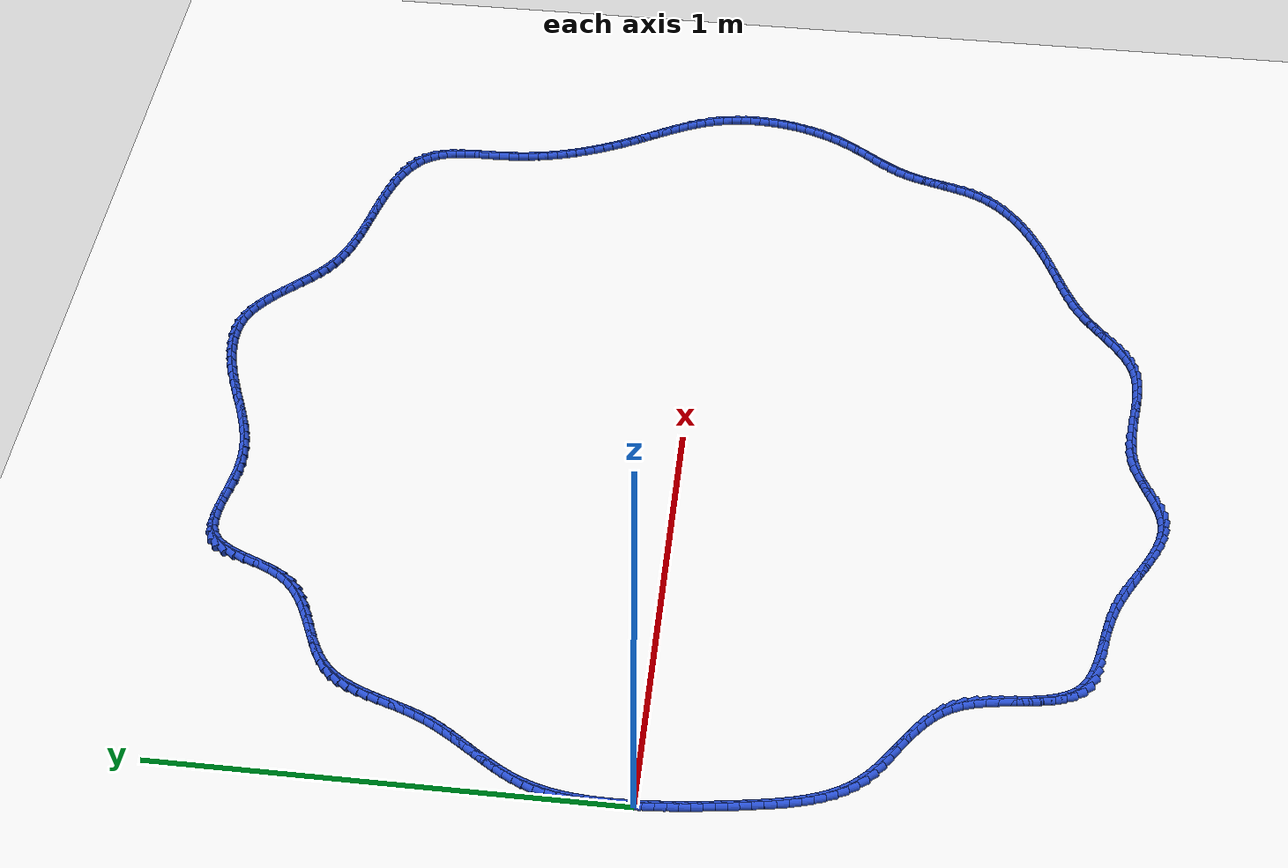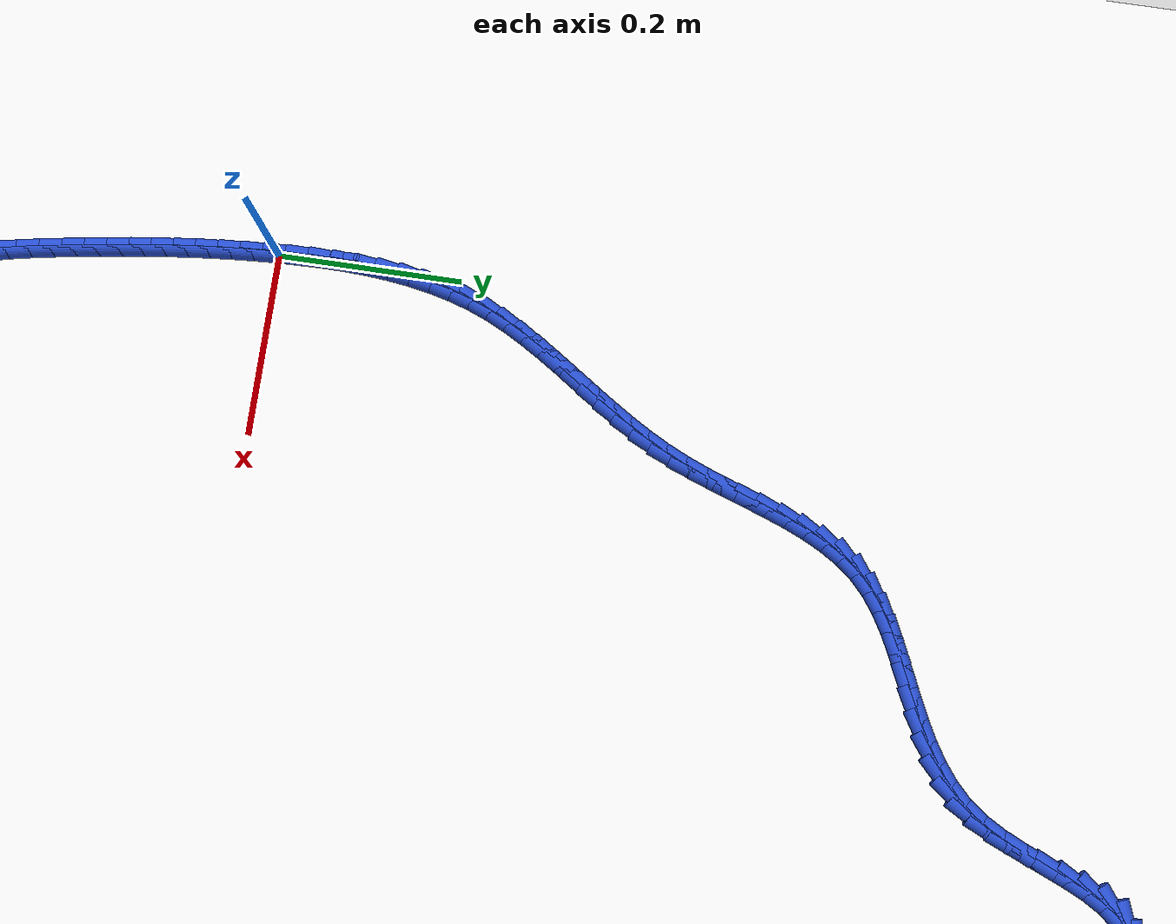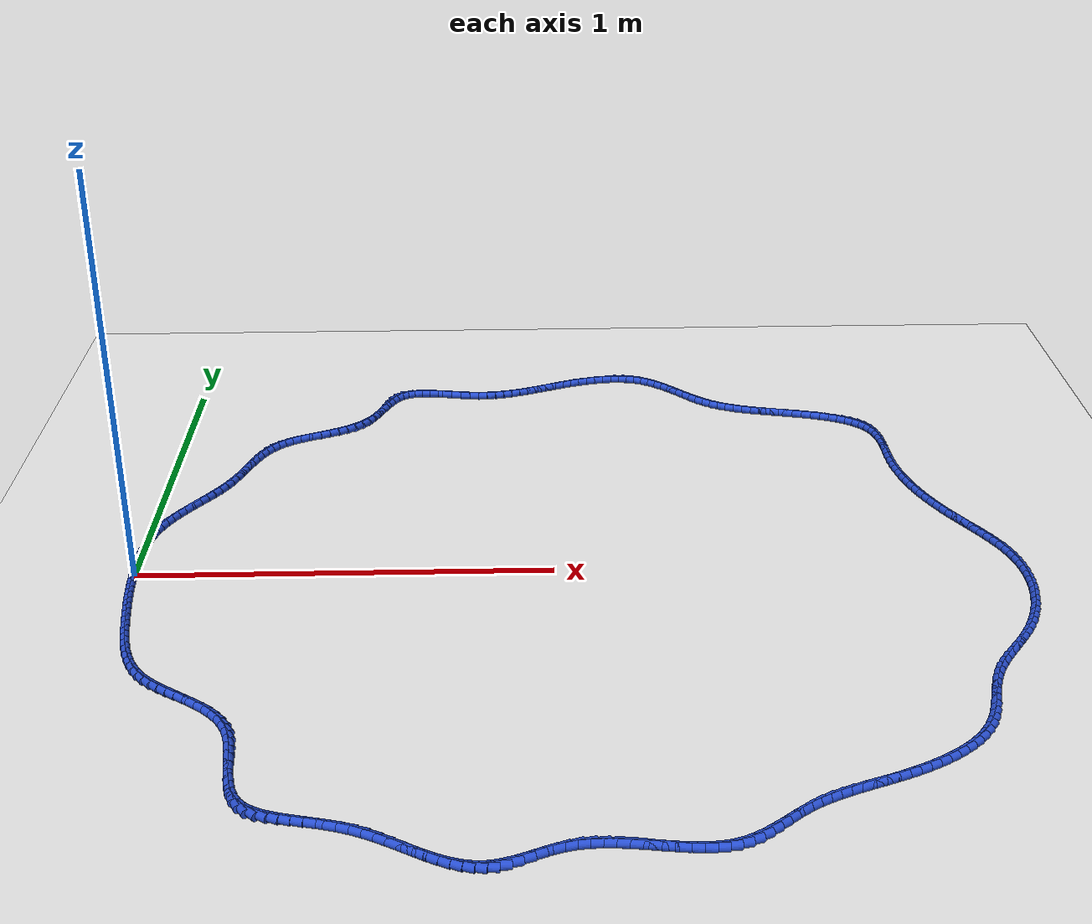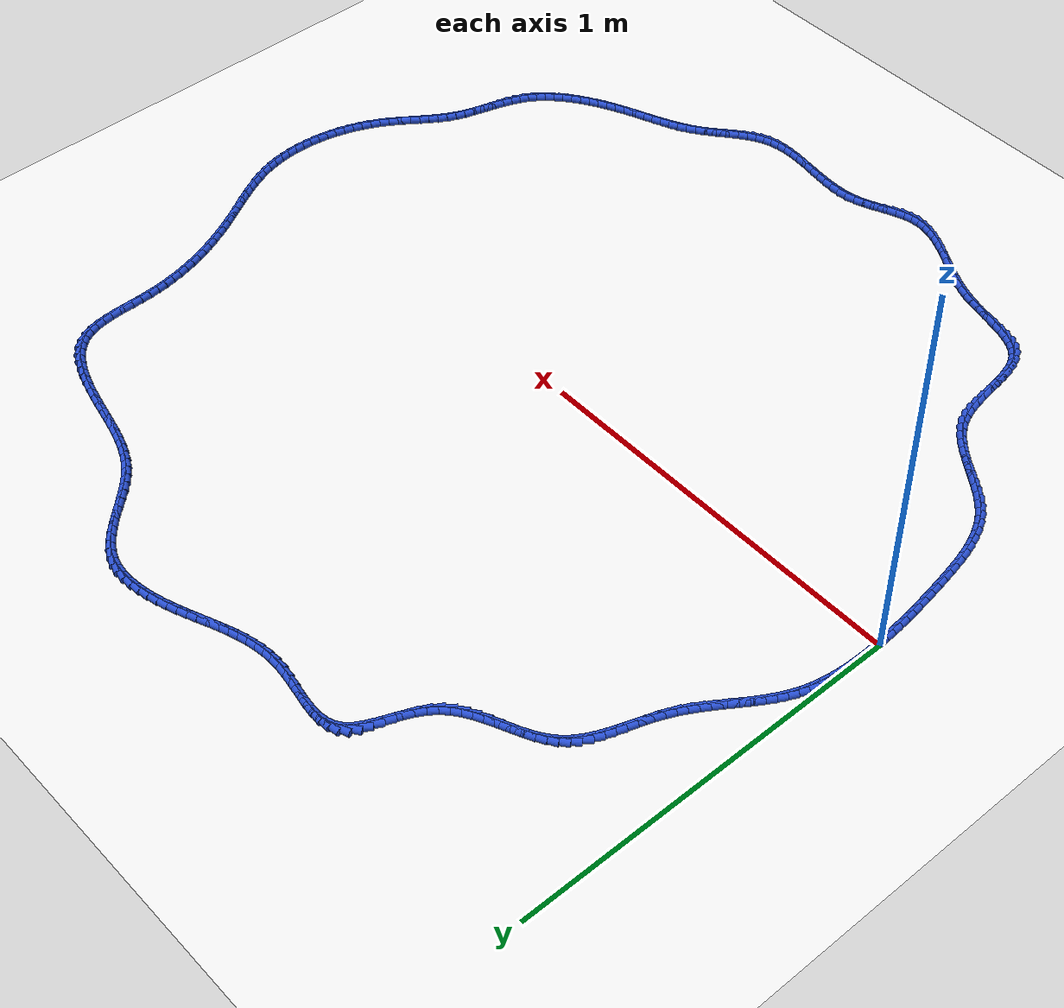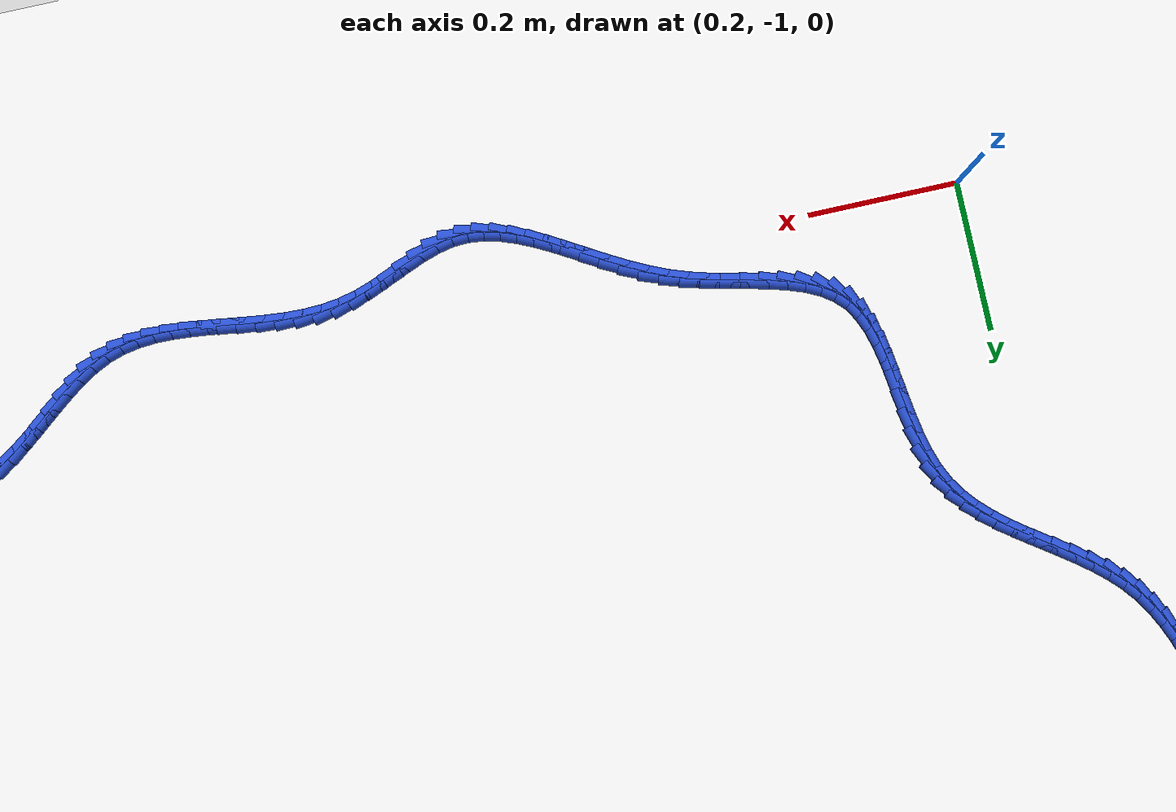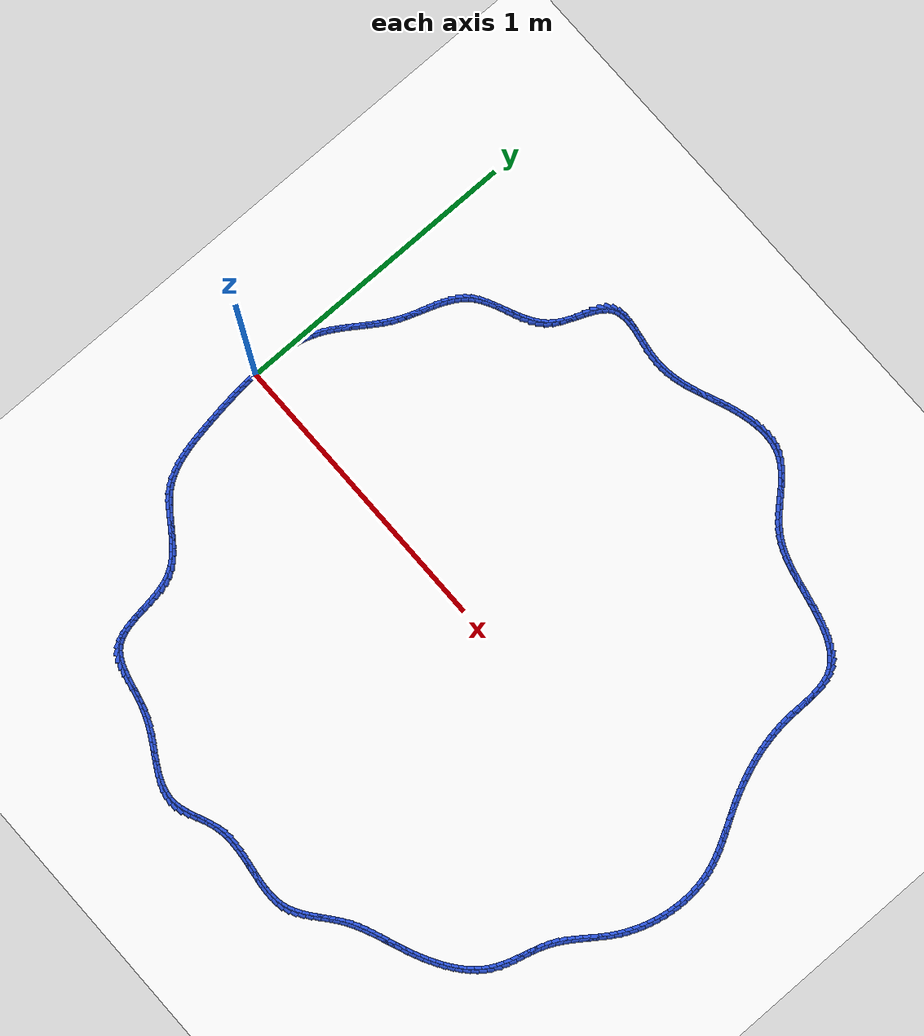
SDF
<sdf version="1.6">
 <world name="default">
  <light name="sun" type="directional">
   <pose>0 0 10 0 -0 0</pose>
   <diffuse>0.8 0.8 0.8 1</diffuse>
   <specular>0.2 0.2 0.2 1</specular>
   <attenuation>
    <range>1000</range>
    <constant>0.9</constant>
    <linear>0.01</linear>
    <quadratic>0.001</quadratic>
   </attenuation>
   <direction>-0.5 0.1 -0.9</direction>
  </light>
  <model name="ground_plane">
   <static>1</static>
   <link name="link">
    <collision name="collision">
     <geometry><plane><normal>0 0 1</normal><size>100 100</size></plane></geometry>
     <surface><friction><ode><mu>100</mu><mu2>50</mu2></ode></friction></surface>
    </collision>
    <visual name="visual">
     <cast_shadows>0</cast_shadows>
     <geometry><plane><normal>0 0 1</normal><size>100 100</size></plane></geometry>
     <material>
      <script><uri>file://media/materials/scripts/gazebo.material</uri><name>Gazebo/WhiteGlow</name></script>
     </material>
    </visual>
   </link>
  </model>
  <gravity>0 0 -9.8</gravity>
  <magnetic_field>6e-06 2.3e-05 -4.2e-05</magnetic_field>
  <atmosphere type="adiabatic"/>
  <physics name="default_physics" default="0" type="ode">
   <max_step_size>0.001</max_step_size>
   <real_time_factor>1</real_time_factor>
   <real_time_update_rate>1000</real_time_update_rate>
  </physics>
  <scene><ambient>0.4 0.4 0.4 1</ambient><background>0.7 0.7 0.7 1</background><shadows>1</shadows></scene>
  <spherical_coordinates>
   <surface_model>EARTH_WGS84</surface_model>
   <latitude_deg>0</latitude_deg>
   <longitude_deg>0</longitude_deg>
   <elevation>0</elevation>
   <heading_deg>0</heading_deg>
  </spherical_coordinates>
  <model name="line">
   <link name="link_0">
    <pose>-6.342582709040201e-18 6.938893903907228e-17 0.01 0 1.57 -1.5347871412486813</pose>
    <collision name="collision">
     <geometry><cylinder><radius>0.01</radius><length>0.08</length></cylinder></geometry>
    </collision>
    <visual name="visual">
     <material>
      <script><name>Gazebo/Blue</name><uri>file://media/materials/scripts/gazebo.material</uri></script>
     </material>
     <geometry><cylinder><radius>0.01</radius><length>0.08</length></cylinder></geometry>
    </visual>
   </link>
   <link name="link_1">
    <pose>-0.0008799934208136524 0.02442746269897507 0.01 0 1.57 -1.5570395334797742</pose>
    <collision name="collision">
     <geometry><cylinder><radius>0.01</radius><length>0.08</length></cylinder></geometry>
    </collision>
    <visual name="visual">
     <material>
      <script><name>Gazebo/Blue</name><uri>file://media/materials/scripts/gazebo.material</uri></script>
     </material>
     <geometry><cylinder><radius>0.01</radius><length>0.08</length></cylinder></geometry>
    </visual>
   </link>
   <link name="link_2">
    <pose>-0.0012180630915780506 0.04900065619413731 0.01 0 1.57 1.5571608358764597</pose>
    <collision name="collision">
     <geometry><cylinder><radius>0.01</radius><length>0.08</length></cylinder></geometry>
    </collision>
    <visual name="visual">
     <material>
      <script><name>Gazebo/Blue</name><uri>file://media/materials/scripts/gazebo.material</uri></script>
     </material>
     <geometry><cylinder><radius>0.01</radius><length>0.08</length></cylinder></geometry>
    </visual>
   </link>
   <link name="link_3">
    <pose>-0.0008824679000233301 0.07361102003155427 0.01 0 1.57 1.524332283293334</pose>
    <collision name="collision">
     <geometry><cylinder><radius>0.01</radius><length>0.08</length></cylinder></geometry>
    </collision>
    <visual name="visual">
     <material>
      <script><name>Gazebo/Blue</name><uri>file://media/materials/scripts/gazebo.material</uri></script>
     </material>
     <geometry><cylinder><radius>0.01</radius><length>0.08</length></cylinder></geometry>
    </visual>
   </link>
   <link name="link_4">
    <pose>0.00025853326612037923 0.0981499937572934 0.01 0 1.57 1.4856891240640355</pose>
    <collision name="collision">
     <geometry><cylinder><radius>0.01</radius><length>0.08</length></cylinder></geometry>
    </collision>
    <visual name="visual">
     <material>
      <script><name>Gazebo/Blue</name><uri>file://media/materials/scripts/gazebo.material</uri></script>
     </material>
     <geometry><cylinder><radius>0.01</radius><length>0.08</length></cylinder></geometry>
    </visual>
   </link>
   <link name="link_5">
    <pose>0.0023366815191229492 0.12250901691742223 0.01 0 1.57 1.44079133324287</pose>
    <collision name="collision">
     <geometry><cylinder><radius>0.01</radius><length>0.08</length></cylinder></geometry>
    </collision>
    <visual name="visual">
     <material>
      <script><name>Gazebo/Blue</name><uri>file://media/materials/scripts/gazebo.material</uri></script>
     </material>
     <geometry><cylinder><radius>0.01</radius><length>0.08</length></cylinder></geometry>
    </visual>
   </link>
   <link name="link_6">
    <pose>0.00548371797125425 0.14657952905800825 0.01 0 1.57 1.389168631819509</pose>
    <collision name="collision">
     <geometry><cylinder><radius>0.01</radius><length>0.08</length></cylinder></geometry>
    </collision>
    <visual name="visual">
     <material>
      <script><name>Gazebo/Blue</name><uri>file://media/materials/scripts/gazebo.material</uri></script>
     </material>
     <geometry><cylinder><radius>0.01</radius><length>0.08</length></cylinder></geometry>
    </visual>
   </link>
   <link name="link_7">
    <pose>0.009831383734784146 0.1702529697251189 0.01 0 1.57 1.3303693170853053</pose>
    <collision name="collision">
     <geometry><cylinder><radius>0.01</radius><length>0.08</length></cylinder></geometry>
    </collision>
    <visual name="visual">
     <material>
      <script><name>Gazebo/Blue</name><uri>file://media/materials/scripts/gazebo.material</uri></script>
     </material>
     <geometry><cylinder><radius>0.01</radius><length>0.08</length></cylinder></geometry>
    </visual>
   </link>
   <link name="link_8">
    <pose>0.015511419921982517 0.19342077846482172 0.01 0 1.57 1.2640325954095852</pose>
    <collision name="collision">
     <geometry><cylinder><radius>0.01</radius><length>0.08</length></cylinder></geometry>
    </collision>
    <visual name="visual">
     <material>
      <script><name>Gazebo/Blue</name><uri>file://media/materials/scripts/gazebo.material</uri></script>
     </material>
     <geometry><cylinder><radius>0.01</radius><length>0.08</length></cylinder></geometry>
    </visual>
   </link>
   <link name="link_9">
    <pose>0.022655567645119223 0.21597439482318412 0.01 0 1.57 1.1911125752542058</pose>
    <collision name="collision">
     <geometry><cylinder><radius>0.01</radius><length>0.08</length></cylinder></geometry>
    </collision>
    <visual name="visual">
     <material>
      <script><name>Gazebo/Blue</name><uri>file://media/materials/scripts/gazebo.material</uri></script>
     </material>
     <geometry><cylinder><radius>0.01</radius><length>0.08</length></cylinder></geometry>
    </visual>
   </link>
   <link name="link_10">
    <pose>0.0313729467780515 0.23781994056765074 0.01 0 1.57 1.1234086189482186</pose>
    <collision name="collision">
     <geometry><cylinder><radius>0.01</radius><length>0.08</length></cylinder></geometry>
    </collision>
    <visual name="visual">
     <material>
      <script><name>Gazebo/Blue</name><uri>file://media/materials/scripts/gazebo.material</uri></script>
     </material>
     <geometry><cylinder><radius>0.01</radius><length>0.08</length></cylinder></geometry>
    </visual>
   </link>
   <link name="link_11">
    <pose>0.04154222121569546 0.25901311396712695 0.01 0 1.57 1.0683558751640316</pose>
    <collision name="collision">
     <geometry><cylinder><radius>0.01</radius><length>0.08</length></cylinder></geometry>
    </collision>
    <visual name="visual">
     <material>
      <script><name>Gazebo/Blue</name><uri>file://media/materials/scripts/gazebo.material</uri></script>
     </material>
     <geometry><cylinder><radius>0.01</radius><length>0.08</length></cylinder></geometry>
    </visual>
   </link>
   <link name="link_12">
    <pose>0.05290748553909749 0.2796969549479801 0.01 0 1.57 1.0263164397584597</pose>
    <collision name="collision">
     <geometry><cylinder><radius>0.01</radius><length>0.08</length></cylinder></geometry>
    </collision>
    <visual name="visual">
     <material>
      <script><name>Gazebo/Blue</name><uri>file://media/materials/scripts/gazebo.material</uri></script>
     </material>
     <geometry><cylinder><radius>0.01</radius><length>0.08</length></cylinder></geometry>
    </visual>
   </link>
   <link name="link_13">
    <pose>0.06521114805718943 0.30001559790452914 0.01 0 1.57 0.9971879001701517</pose>
    <collision name="collision">
     <geometry><cylinder><radius>0.01</radius><length>0.08</length></cylinder></geometry>
    </collision>
    <visual name="visual">
     <material>
      <script><name>Gazebo/Blue</name><uri>file://media/materials/scripts/gazebo.material</uri></script>
     </material>
     <geometry><cylinder><radius>0.01</radius><length>0.08</length></cylinder></geometry>
    </visual>
   </link>
   <link name="link_14">
    <pose>0.07819561707890317 0.32011317723109406 0.01 0 1.57 0.9807016805812409</pose>
    <collision name="collision">
     <geometry><cylinder><radius>0.01</radius><length>0.08</length></cylinder></geometry>
    </collision>
    <visual name="visual">
     <material>
      <script><name>Gazebo/Blue</name><uri>file://media/materials/scripts/gazebo.material</uri></script>
     </material>
     <geometry><cylinder><radius>0.01</radius><length>0.08</length></cylinder></geometry>
    </visual>
   </link>
   <link name="link_15">
    <pose>0.0916033009131706 0.3401338273219942 0.01 0 1.57 0.9765678655862139</pose>
    <collision name="collision">
     <geometry><cylinder><radius>0.01</radius><length>0.08</length></cylinder></geometry>
    </collision>
    <visual name="visual">
     <material>
      <script><name>Gazebo/Blue</name><uri>file://media/materials/scripts/gazebo.material</uri></script>
     </material>
     <geometry><cylinder><radius>0.01</radius><length>0.08</length></cylinder></geometry>
    </visual>
   </link>
   <link name="link_16">
    <pose>0.10517660786892358 0.360221682571549 0.01 0 1.57 0.9845507665978943</pose>
    <collision name="collision">
     <geometry><cylinder><radius>0.01</radius><length>0.08</length></cylinder></geometry>
    </collision>
    <visual name="visual">
     <material>
      <script><name>Gazebo/Blue</name><uri>file://media/materials/scripts/gazebo.material</uri></script>
     </material>
     <geometry><cylinder><radius>0.01</radius><length>0.08</length></cylinder></geometry>
    </visual>
   </link>
   <link name="link_17">
    <pose>0.11865794625509402 0.3805208773740781 0.01 0 1.57 1.0044842572842192</pose>
    <collision name="collision">
     <geometry><cylinder><radius>0.01</radius><length>0.08</length></cylinder></geometry>
    </collision>
    <visual name="visual">
     <material>
      <script><name>Gazebo/Blue</name><uri>file://media/materials/scripts/gazebo.material</uri></script>
     </material>
     <geometry><cylinder><radius>0.01</radius><length>0.08</length></cylinder></geometry>
    </visual>
   </link>
   <link name="link_18">
    <pose>0.13178972438061373 0.40117554612390083 0.01 0 1.57 1.0362346468489319</pose>
    <collision name="collision">
     <geometry><cylinder><radius>0.01</radius><length>0.08</length></cylinder></geometry>
    </collision>
    <visual name="visual">
     <material>
      <script><name>Gazebo/Blue</name><uri>file://media/materials/scripts/gazebo.material</uri></script>
     </material>
     <geometry><cylinder><radius>0.01</radius><length>0.08</length></cylinder></geometry>
    </visual>
   </link>
   <link name="link_19">
    <pose>0.1443143505544146 0.42232982321533674 0.01 0 1.57 1.0796157289752024</pose>
    <collision name="collision">
     <geometry><cylinder><radius>0.01</radius><length>0.08</length></cylinder></geometry>
    </collision>
    <visual name="visual">
     <material>
      <script><name>Gazebo/Blue</name><uri>file://media/materials/scripts/gazebo.material</uri></script>
     </material>
     <geometry><cylinder><radius>0.01</radius><length>0.08</length></cylinder></geometry>
    </visual>
   </link>
   <link name="link_20">
    <pose>0.1559742330854286 0.44412784304270536 0.01 0 1.57 1.134026885642316</pose>
    <collision name="collision">
     <geometry><cylinder><radius>0.01</radius><length>0.08</length></cylinder></geometry>
    </collision>
    <visual name="visual">
     <material>
      <script><name>Gazebo/Blue</name><uri>file://media/materials/scripts/gazebo.material</uri></script>
     </material>
     <geometry><cylinder><radius>0.01</radius><length>0.08</length></cylinder></geometry>
    </visual>
   </link>
   <link name="link_21">
    <pose>0.16651658963488622 0.4667102219870624 0.01 0 1.57 1.186977805018994</pose>
    <collision name="collision">
     <geometry><cylinder><radius>0.01</radius><length>0.08</length></cylinder></geometry>
    </collision>
    <visual name="visual">
     <material>
      <script><name>Gazebo/Blue</name><uri>file://media/materials/scripts/gazebo.material</uri></script>
     </material>
     <geometry><cylinder><radius>0.01</radius><length>0.08</length></cylinder></geometry>
    </visual>
   </link>
   <link name="link_22">
    <pose>0.1759366910279049 0.4900361269812874 0.01 0 1.57 1.2214753635690403</pose>
    <collision name="collision">
     <geometry><cylinder><radius>0.01</radius><length>0.08</length></cylinder></geometry>
    </collision>
    <visual name="visual">
     <material>
      <script><name>Gazebo/Blue</name><uri>file://media/materials/scripts/gazebo.material</uri></script>
     </material>
     <geometry><cylinder><radius>0.01</radius><length>0.08</length></cylinder></geometry>
    </visual>
   </link>
   <link name="link_23">
    <pose>0.18459264817947837 0.5137993095406426 0.01 0 1.57 1.236992576579386</pose>
    <collision name="collision">
     <geometry><cylinder><radius>0.01</radius><length>0.08</length></cylinder></geometry>
    </collision>
    <visual name="visual">
     <material>
      <script><name>Gazebo/Blue</name><uri>file://media/materials/scripts/gazebo.material</uri></script>
     </material>
     <geometry><cylinder><radius>0.01</radius><length>0.08</length></cylinder></geometry>
    </visual>
   </link>
   <link name="link_24">
    <pose>0.19287138479466207 0.537672444791865 0.01 0 1.57 1.2337855205060173</pose>
    <collision name="collision">
     <geometry><cylinder><radius>0.01</radius><length>0.08</length></cylinder></geometry>
    </collision>
    <visual name="visual">
     <material>
      <script><name>Gazebo/Blue</name><uri>file://media/materials/scripts/gazebo.material</uri></script>
     </material>
     <geometry><cylinder><radius>0.01</radius><length>0.08</length></cylinder></geometry>
    </visual>
   </link>
   <link name="link_25">
    <pose>0.2011598245785113 0.5613282078616916 0.01 0 1.57 1.2113271992038253</pose>
    <collision name="collision">
     <geometry><cylinder><radius>0.01</radius><length>0.08</length></cylinder></geometry>
    </collision>
    <visual name="visual">
     <material>
      <script><name>Gazebo/Blue</name><uri>file://media/materials/scripts/gazebo.material</uri></script>
     </material>
     <geometry><cylinder><radius>0.01</radius><length>0.08</length></cylinder></geometry>
    </visual>
   </link>
   <link name="link_26">
    <pose>0.20984489123608158 0.5844392738768591 0.01 0 1.57 1.1682774912918</pose>
    <collision name="collision">
     <geometry><cylinder><radius>0.01</radius><length>0.08</length></cylinder></geometry>
    </collision>
    <visual name="visual">
     <material>
      <script><name>Gazebo/Blue</name><uri>file://media/materials/scripts/gazebo.material</uri></script>
     </material>
     <geometry><cylinder><radius>0.01</radius><length>0.08</length></cylinder></geometry>
    </visual>
   </link>
   <link name="link_27">
    <pose>0.21931350847242823 0.6066783179641042 0.01 0 1.57 1.102624989114232</pose>
    <collision name="collision">
     <geometry><cylinder><radius>0.01</radius><length>0.08</length></cylinder></geometry>
    </collision>
    <visual name="visual">
     <material>
      <script><name>Gazebo/Blue</name><uri>file://media/materials/scripts/gazebo.material</uri></script>
     </material>
     <geometry><cylinder><radius>0.01</radius><length>0.08</length></cylinder></geometry>
    </visual>
   </link>
   <link name="link_28">
    <pose>0.22995259999260664 0.6277180152501639 0.01 0 1.57 1.012165742764886</pose>
    <collision name="collision">
     <geometry><cylinder><radius>0.01</radius><length>0.08</length></cylinder></geometry>
    </collision>
    <visual name="visual">
     <material>
      <script><name>Gazebo/Blue</name><uri>file://media/materials/scripts/gazebo.material</uri></script>
     </material>
     <geometry><cylinder><radius>0.01</radius><length>0.08</length></cylinder></geometry>
    </visual>
   </link>
   <link name="link_29">
    <pose>0.2421490895016723 0.6472310408617751 0.01 0 1.57 0.8955863764980082</pose>
    <collision name="collision">
     <geometry><cylinder><radius>0.01</radius><length>0.08</length></cylinder></geometry>
    </collision>
    <visual name="visual">
     <material>
      <script><name>Gazebo/Blue</name><uri>file://media/materials/scripts/gazebo.material</uri></script>
     </material>
     <geometry><cylinder><radius>0.01</radius><length>0.08</length></cylinder></geometry>
    </visual>
   </link>
   <link name="link_30">
    <pose>0.25628990070468044 0.6648900699256743 0.01 0 1.57 0.7562515798991263</pose>
    <collision name="collision">
     <geometry><cylinder><radius>0.01</radius><length>0.08</length></cylinder></geometry>
    </collision>
    <visual name="visual">
     <material>
      <script><name>Gazebo/Blue</name><uri>file://media/materials/scripts/gazebo.material</uri></script>
     </material>
     <geometry><cylinder><radius>0.01</radius><length>0.08</length></cylinder></geometry>
    </visual>
   </link>
   <link name="link_31">
    <pose>0.2727296673933222 0.6803983951115162 0.01 0 1.57 0.6271028827277211</pose>
    <collision name="collision">
     <geometry><cylinder><radius>0.01</radius><length>0.08</length></cylinder></geometry>
    </collision>
    <visual name="visual">
     <material>
      <script><name>Gazebo/Blue</name><uri>file://media/materials/scripts/gazebo.material</uri></script>
     </material>
     <geometry><cylinder><radius>0.01</radius><length>0.08</length></cylinder></geometry>
    </visual>
   </link>
   <link name="link_32">
    <pose>0.2913592825335145 0.6938990316882535 0.01 0 1.57 0.5312506755514216</pose>
    <collision name="collision">
     <geometry><cylinder><radius>0.01</radius><length>0.08</length></cylinder></geometry>
    </collision>
    <visual name="visual">
     <material>
      <script><name>Gazebo/Blue</name><uri>file://media/materials/scripts/gazebo.material</uri></script>
     </material>
     <geometry><cylinder><radius>0.01</radius><length>0.08</length></cylinder></geometry>
    </visual>
   </link>
   <link name="link_33">
    <pose>0.3117223252994584 0.7058643205196048 0.01 0 1.57 0.46713311786602135</pose>
    <collision name="collision">
     <geometry><cylinder><radius>0.01</radius><length>0.08</length></cylinder></geometry>
    </collision>
    <visual name="visual">
     <material>
      <script><name>Gazebo/Blue</name><uri>file://media/materials/scripts/gazebo.material</uri></script>
     </material>
     <geometry><cylinder><radius>0.01</radius><length>0.08</length></cylinder></geometry>
    </visual>
   </link>
   <link name="link_34">
    <pose>0.3333539821349543 0.7167745605204731 0.01 0 1.57 0.4316970277547114</pose>
    <collision name="collision">
     <geometry><cylinder><radius>0.01</radius><length>0.08</length></cylinder></geometry>
    </collision>
    <visual name="visual">
     <material>
      <script><name>Gazebo/Blue</name><uri>file://media/materials/scripts/gazebo.material</uri></script>
     </material>
     <geometry><cylinder><radius>0.01</radius><length>0.08</length></cylinder></geometry>
    </visual>
   </link>
   <link name="link_35">
    <pose>0.355789439483802 0.7271100506057604 0.01 0 1.57 0.4225814623082304</pose>
    <collision name="collision">
     <geometry><cylinder><radius>0.01</radius><length>0.08</length></cylinder></geometry>
    </collision>
    <visual name="visual">
     <material>
      <script><name>Gazebo/Blue</name><uri>file://media/materials/scripts/gazebo.material</uri></script>
     </material>
     <geometry><cylinder><radius>0.01</radius><length>0.08</length></cylinder></geometry>
    </visual>
   </link>
   <link name="link_36">
    <pose>0.3785638837898013 0.7373510896903691 0.01 0 1.57 0.4387110607294869</pose>
    <collision name="collision">
     <geometry><cylinder><radius>0.01</radius><length>0.08</length></cylinder></geometry>
    </collision>
    <visual name="visual">
     <material>
      <script><name>Gazebo/Blue</name><uri>file://media/materials/scripts/gazebo.material</uri></script>
     </material>
     <geometry><cylinder><radius>0.01</radius><length>0.08</length></cylinder></geometry>
    </visual>
   </link>
   <link name="link_37">
    <pose>0.40121250149675247 0.7479779766892014 0.01 0 1.57 0.48033562951393916</pose>
    <collision name="collision">
     <geometry><cylinder><radius>0.01</radius><length>0.08</length></cylinder></geometry>
    </collision>
    <visual name="visual">
     <material>
      <script><name>Gazebo/Blue</name><uri>file://media/materials/scripts/gazebo.material</uri></script>
     </material>
     <geometry><cylinder><radius>0.01</radius><length>0.08</length></cylinder></geometry>
    </visual>
   </link>
   <link name="link_38">
    <pose>0.4232704790484553 0.7594710105171598 0.01 0 1.57 0.5487089889923414</pose>
    <collision name="collision">
     <geometry><cylinder><radius>0.01</radius><length>0.08</length></cylinder></geometry>
    </collision>
    <visual name="visual">
     <material>
      <script><name>Gazebo/Blue</name><uri>file://media/materials/scripts/gazebo.material</uri></script>
     </material>
     <geometry><cylinder><radius>0.01</radius><length>0.08</length></cylinder></geometry>
    </visual>
   </link>
   <link name="link_39">
    <pose>0.4442730028887098 0.7723104900891468 0.01 0 1.57 0.6452900950118969</pose>
    <collision name="collision">
     <geometry><cylinder><radius>0.01</radius><length>0.08</length></cylinder></geometry>
    </collision>
    <visual name="visual">
     <material>
      <script><name>Gazebo/Blue</name><uri>file://media/materials/scripts/gazebo.material</uri></script>
     </material>
     <geometry><cylinder><radius>0.01</radius><length>0.08</length></cylinder></geometry>
    </visual>
   </link>
   <link name="link_40">
    <pose>0.4637552594613158 0.7869767143200641 0.01 0 1.57 0.7702005751366988</pose>
    <collision name="collision">
     <geometry><cylinder><radius>0.01</radius><length>0.08</length></cylinder></geometry>
    </collision>
    <visual name="visual">
     <material>
      <script><name>Gazebo/Blue</name><uri>file://media/materials/scripts/gazebo.material</uri></script>
     </material>
     <geometry><cylinder><radius>0.01</radius><length>0.08</length></cylinder></geometry>
    </visual>
   </link>
   <link name="link_41">
    <pose>0.4812524352100734 0.8039499821248146 0.01 0 1.57 0.9185451669088889</pose>
    <collision name="collision">
     <geometry><cylinder><radius>0.01</radius><length>0.08</length></cylinder></geometry>
    </collision>
    <visual name="visual">
     <material>
      <script><name>Gazebo/Blue</name><uri>file://media/materials/scripts/gazebo.material</uri></script>
     </material>
     <geometry><cylinder><radius>0.01</radius><length>0.08</length></cylinder></geometry>
    </visual>
   </link>
   <link name="link_42">
    <pose>0.4963226224784224 0.8236814887453041 0.01 0 1.57 1.050078902577583</pose>
    <collision name="collision">
     <geometry><cylinder><radius>0.01</radius><length>0.08</length></cylinder></geometry>
    </collision>
    <visual name="visual">
     <material>
      <script><name>Gazebo/Blue</name><uri>file://media/materials/scripts/gazebo.material</uri></script>
     </material>
     <geometry><cylinder><radius>0.01</radius><length>0.08</length></cylinder></geometry>
    </visual>
   </link>
   <link name="link_43">
    <pose>0.5090767464459953 0.845920013611824 0.01 0 1.57 1.133389874532252</pose>
    <collision name="collision">
     <geometry><cylinder><radius>0.01</radius><length>0.08</length></cylinder></geometry>
    </collision>
    <visual name="visual">
     <material>
      <script><name>Gazebo/Blue</name><uri>file://media/materials/scripts/gazebo.material</uri></script>
     </material>
     <geometry><cylinder><radius>0.01</radius><length>0.08</length></cylinder></geometry>
    </visual>
   </link>
   <link name="link_44">
    <pose>0.5201934057085449 0.8696930642670153 0.01 0 1.57 1.1739821972694273</pose>
    <collision name="collision">
     <geometry><cylinder><radius>0.01</radius><length>0.08</length></cylinder></geometry>
    </collision>
    <visual name="visual">
     <material>
      <script><name>Gazebo/Blue</name><uri>file://media/materials/scripts/gazebo.material</uri></script>
     </material>
     <geometry><cylinder><radius>0.01</radius><length>0.08</length></cylinder></geometry>
    </visual>
   </link>
   <link name="link_45">
    <pose>0.5303770735304086 0.8939952725356803 0.01 0 1.57 1.1750167672954164</pose>
    <collision name="collision">
     <geometry><cylinder><radius>0.01</radius><length>0.08</length></cylinder></geometry>
    </collision>
    <visual name="visual">
     <material>
      <script><name>Gazebo/Blue</name><uri>file://media/materials/scripts/gazebo.material</uri></script>
     </material>
     <geometry><cylinder><radius>0.01</radius><length>0.08</length></cylinder></geometry>
    </visual>
   </link>
   <link name="link_46">
    <pose>0.5403322231759249 0.9178212702426218 0.01 0 1.57 1.1340328602919592</pose>
    <collision name="collision">
     <geometry><cylinder><radius>0.01</radius><length>0.08</length></cylinder></geometry>
    </collision>
    <visual name="visual">
     <material>
      <script><name>Gazebo/Blue</name><uri>file://media/materials/scripts/gazebo.material</uri></script>
     </material>
     <geometry><cylinder><radius>0.01</radius><length>0.08</length></cylinder></geometry>
    </visual>
   </link>
   <link name="link_47">
    <pose>0.5507633279094314 0.9401656892126415 0.01 0 1.57 1.041670177382802</pose>
    <collision name="collision">
     <geometry><cylinder><radius>0.01</radius><length>0.08</length></cylinder></geometry>
    </collision>
    <visual name="visual">
     <material>
      <script><name>Gazebo/Blue</name><uri>file://media/materials/scripts/gazebo.material</uri></script>
     </material>
     <geometry><cylinder><radius>0.01</radius><length>0.08</length></cylinder></geometry>
    </visual>
   </link>
   <link name="link_48">
    <pose>0.5623748609952662 0.9600231612705427 0.01 0 1.57 0.8811715492622904</pose>
    <collision name="collision">
     <geometry><cylinder><radius>0.01</radius><length>0.08</length></cylinder></geometry>
    </collision>
    <visual name="visual">
     <material>
      <script><name>Gazebo/Blue</name><uri>file://media/materials/scripts/gazebo.material</uri></script>
     </material>
     <geometry><cylinder><radius>0.01</radius><length>0.08</length></cylinder></geometry>
    </visual>
   </link>
   <link name="link_49">
    <pose>0.575871295697767 0.9763883182411265 0.01 0 1.57 0.6360557288784366</pose>
    <collision name="collision">
     <geometry><cylinder><radius>0.01</radius><length>0.08</length></cylinder></geometry>
    </collision>
    <visual name="visual">
     <material>
      <script><name>Gazebo/Blue</name><uri>file://media/materials/scripts/gazebo.material</uri></script>
     </material>
     <geometry><cylinder><radius>0.01</radius><length>0.08</length></cylinder></geometry>
    </visual>
   </link>
   <link name="link_50">
    <pose>0.5919525045512037 0.9882631810851074 0.01 0 1.57 0.35495236998822727</pose>
    <collision name="collision">
     <geometry><cylinder><radius>0.01</radius><length>0.08</length></cylinder></geometry>
    </collision>
    <visual name="visual">
     <material>
      <script><name>Gazebo/Blue</name><uri>file://media/materials/scripts/gazebo.material</uri></script>
     </material>
     <geometry><cylinder><radius>0.01</radius><length>0.08</length></cylinder></geometry>
    </visual>
   </link>
   <link name="link_51">
    <pose>0.6109180104026382 0.9952927639853123 0.01 0 1.57 0.13724463481481647</pose>
    <collision name="collision">
     <geometry><cylinder><radius>0.01</radius><length>0.08</length></cylinder></geometry>
    </collision>
    <visual name="visual">
     <material>
      <script><name>Gazebo/Blue</name><uri>file://media/materials/scripts/gazebo.material</uri></script>
     </material>
     <geometry><cylinder><radius>0.01</radius><length>0.08</length></cylinder></geometry>
    </visual>
   </link>
   <link name="link_52">
    <pose>0.6323622586606645 0.9982544911862857 0.01 0 1.57 -0.009105523998116686</pose>
    <collision name="collision">
     <geometry><cylinder><radius>0.01</radius><length>0.08</length></cylinder></geometry>
    </collision>
    <visual name="visual">
     <material>
      <script><name>Gazebo/Blue</name><uri>file://media/materials/scripts/gazebo.material</uri></script>
     </material>
     <geometry><cylinder><radius>0.01</radius><length>0.08</length></cylinder></geometry>
    </visual>
   </link>
   <link name="link_53">
    <pose>0.6558079591808439 0.998040999897286 0.01 0 1.57 -0.09963242278142019</pose>
    <collision name="collision">
     <geometry><cylinder><radius>0.01</radius><length>0.08</length></cylinder></geometry>
    </collision>
    <visual name="visual">
     <material>
      <script><name>Gazebo/Blue</name><uri>file://media/materials/scripts/gazebo.material</uri></script>
     </material>
     <geometry><cylinder><radius>0.01</radius><length>0.08</length></cylinder></geometry>
    </visual>
   </link>
   <link name="link_54">
    <pose>0.6807778218187377 0.9955449273275712 0.01 0 1.57 -0.14826988094005367</pose>
    <collision name="collision">
     <geometry><cylinder><radius>0.01</radius><length>0.08</length></cylinder></geometry>
    </collision>
    <visual name="visual">
     <material>
      <script><name>Gazebo/Blue</name><uri>file://media/materials/scripts/gazebo.material</uri></script>
     </material>
     <geometry><cylinder><radius>0.01</radius><length>0.08</length></cylinder></geometry>
    </visual>
   </link>
   <link name="link_55">
    <pose>0.7067945564299073 0.9916589106863991 0.01 0 1.57 -0.16340143523661366</pose>
    <collision name="collision">
     <geometry><cylinder><radius>0.01</radius><length>0.08</length></cylinder></geometry>
    </collision>
    <visual name="visual">
     <material>
      <script><name>Gazebo/Blue</name><uri>file://media/materials/scripts/gazebo.material</uri></script>
     </material>
     <geometry><cylinder><radius>0.01</radius><length>0.08</length></cylinder></geometry>
    </visual>
   </link>
   <link name="link_56">
    <pose>0.7333808728699132 0.9872755871830278 0.01 0 1.57 -0.14838409437230246</pose>
    <collision name="collision">
     <geometry><cylinder><radius>0.01</radius><length>0.08</length></cylinder></geometry>
    </collision>
    <visual name="visual">
     <material>
      <script><name>Gazebo/Blue</name><uri>file://media/materials/scripts/gazebo.material</uri></script>
     </material>
     <geometry><cylinder><radius>0.01</radius><length>0.08</length></cylinder></geometry>
    </visual>
   </link>
   <link name="link_57">
    <pose>0.7600594809943166 0.983287594026715 0.01 0 1.57 -0.1023288504444193</pose>
    <collision name="collision">
     <geometry><cylinder><radius>0.01</radius><length>0.08</length></cylinder></geometry>
    </collision>
    <visual name="visual">
     <material>
      <script><name>Gazebo/Blue</name><uri>file://media/materials/scripts/gazebo.material</uri></script>
     </material>
     <geometry><cylinder><radius>0.01</radius><length>0.08</length></cylinder></geometry>
    </visual>
   </link>
   <link name="link_58">
    <pose>0.786353090658679 0.9805875684267186 0.01 0 1.57 -0.025306620141647373</pose>
    <collision name="collision">
     <geometry><cylinder><radius>0.01</radius><length>0.08</length></cylinder></geometry>
    </collision>
    <visual name="visual">
     <material>
      <script><name>Gazebo/Blue</name><uri>file://media/materials/scripts/gazebo.material</uri></script>
     </material>
     <geometry><cylinder><radius>0.01</radius><length>0.08</length></cylinder></geometry>
    </visual>
   </link>
   <link name="link_59">
    <pose>0.8118502905985796 0.9799421826935569 0.01 0 1.57 0.058012595947376656</pose>
    <collision name="collision">
     <geometry><cylinder><radius>0.01</radius><length>0.08</length></cylinder></geometry>
    </collision>
    <visual name="visual">
     <material>
      <script><name>Gazebo/Blue</name><uri>file://media/materials/scripts/gazebo.material</uri></script>
     </material>
     <geometry><cylinder><radius>0.01</radius><length>0.08</length></cylinder></geometry>
    </visual>
   </link>
   <link name="link_60">
    <pose>0.8365280944329405 0.9813754143456705 0.01 0 1.57 0.13532036666044464</pose>
    <collision name="collision">
     <geometry><cylinder><radius>0.01</radius><length>0.08</length></cylinder></geometry>
    </collision>
    <visual name="visual">
     <material>
      <script><name>Gazebo/Blue</name><uri>file://media/materials/scripts/gazebo.material</uri></script>
     </material>
     <geometry><cylinder><radius>0.01</radius><length>0.08</length></cylinder></geometry>
    </visual>
   </link>
   <link name="link_61">
    <pose>0.8605053832229752 0.9846399807040325 0.01 0 1.57 0.2043333689495089</pose>
    <collision name="collision">
     <geometry><cylinder><radius>0.01</radius><length>0.08</length></cylinder></geometry>
    </collision>
    <visual name="visual">
     <material>
      <script><name>Gazebo/Blue</name><uri>file://media/materials/scripts/gazebo.material</uri></script>
     </material>
     <geometry><cylinder><radius>0.01</radius><length>0.08</length></cylinder></geometry>
    </visual>
   </link>
   <link name="link_62">
    <pose>0.8839012470533677 0.9894881994225249 0.01 0 1.57 0.26339219855944657</pose>
    <collision name="collision">
     <geometry><cylinder><radius>0.01</radius><length>0.08</length></cylinder></geometry>
    </collision>
    <visual name="visual">
     <material>
      <script><name>Gazebo/Blue</name><uri>file://media/materials/scripts/gazebo.material</uri></script>
     </material>
     <geometry><cylinder><radius>0.01</radius><length>0.08</length></cylinder></geometry>
    </visual>
   </link>
   <link name="link_63">
    <pose>0.9068347760088034 0.99567238815503 0.01 0 1.57 0.3114521354325239</pose>
    <collision name="collision">
     <geometry><cylinder><radius>0.01</radius><length>0.08</length></cylinder></geometry>
    </collision>
    <visual name="visual">
     <material>
      <script><name>Gazebo/Blue</name><uri>file://media/materials/scripts/gazebo.material</uri></script>
     </material>
     <geometry><cylinder><radius>0.01</radius><length>0.08</length></cylinder></geometry>
    </visual>
   </link>
   <link name="link_64">
    <pose>0.9294250601739663 1.00294486455543 0.01 0 1.57 0.3479787777669362</pose>
    <collision name="collision">
     <geometry><cylinder><radius>0.01</radius><length>0.08</length></cylinder></geometry>
    </collision>
    <visual name="visual">
     <material>
      <script><name>Gazebo/Blue</name><uri>file://media/materials/scripts/gazebo.material</uri></script>
     </material>
     <geometry><cylinder><radius>0.01</radius><length>0.08</length></cylinder></geometry>
    </visual>
   </link>
   <link name="link_65">
    <pose>0.9517911896335411 1.0110579462776066 0.01 0 1.57 0.37279889502759167</pose>
    <collision name="collision">
     <geometry><cylinder><radius>0.01</radius><length>0.08</length></cylinder></geometry>
    </collision>
    <visual name="visual">
     <material>
      <script><name>Gazebo/Blue</name><uri>file://media/materials/scripts/gazebo.material</uri></script>
     </material>
     <geometry><cylinder><radius>0.01</radius><length>0.08</length></cylinder></geometry>
    </visual>
   </link>
   <link name="link_66">
    <pose>0.974052254472213 1.0197639509754426 0.01 0 1.57 0.3859593447923466</pose>
    <collision name="collision">
     <geometry><cylinder><radius>0.01</radius><length>0.08</length></cylinder></geometry>
    </collision>
    <visual name="visual">
     <material>
      <script><name>Gazebo/Blue</name><uri>file://media/materials/scripts/gazebo.material</uri></script>
     </material>
     <geometry><cylinder><radius>0.01</radius><length>0.08</length></cylinder></geometry>
    </visual>
   </link>
   <link name="link_67">
    <pose>0.9963273447746659 1.0288151963028198 0.01 0 1.57 0.38762315166648637</pose>
    <collision name="collision">
     <geometry><cylinder><radius>0.01</radius><length>0.08</length></cylinder></geometry>
    </collision>
    <visual name="visual">
     <material>
      <script><name>Gazebo/Blue</name><uri>file://media/materials/scripts/gazebo.material</uri></script>
     </material>
     <geometry><cylinder><radius>0.01</radius><length>0.08</length></cylinder></geometry>
    </visual>
   </link>
   <link name="link_68">
    <pose>1.0187355506255846 1.0379639999136199 0.01 0 1.57 0.37801265278685797</pose>
    <collision name="collision">
     <geometry><cylinder><radius>0.01</radius><length>0.08</length></cylinder></geometry>
    </collision>
    <visual name="visual">
     <material>
      <script><name>Gazebo/Blue</name><uri>file://media/materials/scripts/gazebo.material</uri></script>
     </material>
     <geometry><cylinder><radius>0.01</radius><length>0.08</length></cylinder></geometry>
    </visual>
   </link>
   <link name="link_69">
    <pose>1.0413959621096538 1.046962679461726 0.01 0 1.57 0.35739896019974593</pose>
    <collision name="collision">
     <geometry><cylinder><radius>0.01</radius><length>0.08</length></cylinder></geometry>
    </collision>
    <visual name="visual">
     <material>
      <script><name>Gazebo/Blue</name><uri>file://media/materials/scripts/gazebo.material</uri></script>
     </material>
     <geometry><cylinder><radius>0.01</radius><length>0.08</length></cylinder></geometry>
    </visual>
   </link>
   <link name="link_70">
    <pose>1.064427669311558 1.0555635526010194 0.01 0 1.57 0.3261322489746391</pose>
    <collision name="collision">
     <geometry><cylinder><radius>0.01</radius><length>0.08</length></cylinder></geometry>
    </collision>
    <visual name="visual">
     <material>
      <script><name>Gazebo/Blue</name><uri>file://media/materials/scripts/gazebo.material</uri></script>
     </material>
     <geometry><cylinder><radius>0.01</radius><length>0.08</length></cylinder></geometry>
    </visual>
   </link>
   <link name="link_71">
    <pose>1.087949762315982 1.0635189369853828 0.01 0 1.57 0.28473856860296326</pose>
    <collision name="collision">
     <geometry><cylinder><radius>0.01</radius><length>0.08</length></cylinder></geometry>
    </collision>
    <visual name="visual">
     <material>
      <script><name>Gazebo/Blue</name><uri>file://media/materials/scripts/gazebo.material</uri></script>
     </material>
     <geometry><cylinder><radius>0.01</radius><length>0.08</length></cylinder></geometry>
    </visual>
   </link>
   <link name="link_72">
    <pose>1.1120686810617832 1.070578345602721 0.01 0 1.57 0.23399113808751015</pose>
    <collision name="collision">
     <geometry><cylinder><radius>0.01</radius><length>0.08</length></cylinder></geometry>
    </collision>
    <visual name="visual">
     <material>
      <script><name>Gazebo/Blue</name><uri>file://media/materials/scripts/gazebo.material</uri></script>
     </material>
     <geometry><cylinder><radius>0.01</radius><length>0.08</length></cylinder></geometry>
    </visual>
   </link>
   <link name="link_73">
    <pose>1.136674478790447 1.0764433163095641 0.01 0 1.57 0.1729173757470133</pose>
    <collision name="collision">
     <geometry><cylinder><radius>0.01</radius><length>0.08</length></cylinder></geometry>
    </collision>
    <visual name="visual">
     <material>
      <script><name>Gazebo/Blue</name><uri>file://media/materials/scripts/gazebo.material</uri></script>
     </material>
     <geometry><cylinder><radius>0.01</radius><length>0.08</length></cylinder></geometry>
    </visual>
   </link>
   <link name="link_74">
    <pose>1.1614755834262454 1.0807751187825574 0.01 0 1.57 0.09921704525602507</pose>
    <collision name="collision">
     <geometry><cylinder><radius>0.01</radius><length>0.08</length></cylinder></geometry>
    </collision>
    <visual name="visual">
     <material>
      <script><name>Gazebo/Blue</name><uri>file://media/materials/scripts/gazebo.material</uri></script>
     </material>
     <geometry><cylinder><radius>0.01</radius><length>0.08</length></cylinder></geometry>
    </visual>
   </link>
   <link name="link_75">
    <pose>1.18617479192804 1.0832337742560494 0.01 0 1.57 0.010103713938598272</pose>
    <collision name="collision">
     <geometry><cylinder><radius>0.01</radius><length>0.08</length></cylinder></geometry>
    </collision>
    <visual name="visual">
     <material>
      <script><name>Gazebo/Blue</name><uri>file://media/materials/scripts/gazebo.material</uri></script>
     </material>
     <geometry><cylinder><radius>0.01</radius><length>0.08</length></cylinder></geometry>
    </visual>
   </link>
   <link name="link_76">
    <pose>1.2104749012546938 1.083479303964389 0.01 0 1.57 -0.09745313888400436</pose>
    <collision name="collision">
     <geometry><cylinder><radius>0.01</radius><length>0.08</length></cylinder></geometry>
    </collision>
    <visual name="visual">
     <material>
      <script><name>Gazebo/Blue</name><uri>file://media/materials/scripts/gazebo.material</uri></script>
     </material>
     <geometry><cylinder><radius>0.01</radius><length>0.08</length></cylinder></geometry>
    </visual>
   </link>
   <link name="link_77">
    <pose>1.2340787083650686 1.0811717291419265 0.01 0 1.57 -0.2260805146527173</pose>
    <collision name="collision">
     <geometry><cylinder><radius>0.01</radius><length>0.08</length></cylinder></geometry>
    </collision>
    <visual name="visual">
     <material>
      <script><name>Gazebo/Blue</name><uri>file://media/materials/scripts/gazebo.material</uri></script>
     </material>
     <geometry><cylinder><radius>0.01</radius><length>0.08</length></cylinder></geometry>
    </visual>
   </link>
   <link name="link_78">
    <pose>1.2566890102180275 1.0759710710230097 0.01 0 1.57 -0.3727503701952634</pose>
    <collision name="collision">
     <geometry><cylinder><radius>0.01</radius><length>0.08</length></cylinder></geometry>
    </collision>
    <visual name="visual">
     <material>
      <script><name>Gazebo/Blue</name><uri>file://media/materials/scripts/gazebo.material</uri></script>
     </material>
     <geometry><cylinder><radius>0.01</radius><length>0.08</length></cylinder></geometry>
    </visual>
   </link>
   <link name="link_79">
    <pose>1.2780557138143414 1.0676160344169114 0.01 0 1.57 -0.5076221766810302</pose>
    <collision name="collision">
     <geometry><cylinder><radius>0.01</radius><length>0.08</length></cylinder></geometry>
    </collision>
    <visual name="visual">
     <material>
      <script><name>Gazebo/Blue</name><uri>file://media/materials/scripts/gazebo.material</uri></script>
     </material>
     <geometry><cylinder><radius>0.01</radius><length>0.08</length></cylinder></geometry>
    </visual>
   </link>
   <link name="link_80">
    <pose>1.2982505502266855 1.0563828373136752 0.01 0 1.57 -0.6159407088837092</pose>
    <collision name="collision">
     <geometry><cylinder><radius>0.01</radius><length>0.08</length></cylinder></geometry>
    </collision>
    <visual name="visual">
     <material>
      <script><name>Gazebo/Blue</name><uri>file://media/materials/scripts/gazebo.material</uri></script>
     </material>
     <geometry><cylinder><radius>0.01</radius><length>0.08</length></cylinder></geometry>
    </visual>
   </link>
   <link name="link_81">
    <pose>1.3174797914663856 1.0427724090726684 0.01 0 1.57 -0.6977342186488167</pose>
    <collision name="collision">
     <geometry><cylinder><radius>0.01</radius><length>0.08</length></cylinder></geometry>
    </collision>
    <visual name="visual">
     <material>
      <script><name>Gazebo/Blue</name><uri>file://media/materials/scripts/gazebo.material</uri></script>
     </material>
     <geometry><cylinder><radius>0.01</radius><length>0.08</length></cylinder></geometry>
    </visual>
   </link>
   <link name="link_82">
    <pose>1.335950161943517 1.027286434653326 0.01 0 1.57 -0.7549749041859835</pose>
    <collision name="collision">
     <geometry><cylinder><radius>0.01</radius><length>0.08</length></cylinder></geometry>
    </collision>
    <visual name="visual">
     <material>
      <script><name>Gazebo/Blue</name><uri>file://media/materials/scripts/gazebo.material</uri></script>
     </material>
     <geometry><cylinder><radius>0.01</radius><length>0.08</length></cylinder></geometry>
    </visual>
   </link>
   <link name="link_83">
    <pose>1.3538683860681522 1.0104265990150818 0.01 0 1.57 -0.7899077080704238</pose>
    <collision name="collision">
     <geometry><cylinder><radius>0.01</radius><length>0.08</length></cylinder></geometry>
    </collision>
    <visual name="visual">
     <material>
      <script><name>Gazebo/Blue</name><uri>file://media/materials/scripts/gazebo.material</uri></script>
     </material>
     <geometry><cylinder><radius>0.01</radius><length>0.08</length></cylinder></geometry>
    </visual>
   </link>
   <link name="link_84">
    <pose>1.3714411882503674 0.9926945871173714 0.01 0 1.57 -0.8042046783027027</pose>
    <collision name="collision">
     <geometry><cylinder><radius>0.01</radius><length>0.08</length></cylinder></geometry>
    </collision>
    <visual name="visual">
     <material>
      <script><name>Gazebo/Blue</name><uri>file://media/materials/scripts/gazebo.material</uri></script>
     </material>
     <geometry><cylinder><radius>0.01</radius><length>0.08</length></cylinder></geometry>
    </visual>
   </link>
   <link name="link_85">
    <pose>1.3888752929002357 0.9745920839196293 0.01 0 1.57 -0.7986235692636736</pose>
    <collision name="collision">
     <geometry><cylinder><radius>0.01</radius><length>0.08</length></cylinder></geometry>
    </collision>
    <visual name="visual">
     <material>
      <script><name>Gazebo/Blue</name><uri>file://media/materials/scripts/gazebo.material</uri></script>
     </material>
     <geometry><cylinder><radius>0.01</radius><length>0.08</length></cylinder></geometry>
    </visual>
   </link>
   <link name="link_86">
    <pose>1.4063774244278326 0.95662077438129 0.01 0 1.57 -0.7729127527242137</pose>
    <collision name="collision">
     <geometry><cylinder><radius>0.01</radius><length>0.08</length></cylinder></geometry>
    </collision>
    <visual name="visual">
     <material>
      <script><name>Gazebo/Blue</name><uri>file://media/materials/scripts/gazebo.material</uri></script>
     </material>
     <geometry><cylinder><radius>0.01</radius><length>0.08</length></cylinder></geometry>
    </visual>
   </link>
   <link name="link_87">
    <pose>1.4241543072432323 0.9392823434617882 0.01 0 1.57 -0.7258528964914208</pose>
    <collision name="collision">
     <geometry><cylinder><radius>0.01</radius><length>0.08</length></cylinder></geometry>
    </collision>
    <visual name="visual">
     <material>
      <script><name>Gazebo/Blue</name><uri>file://media/materials/scripts/gazebo.material</uri></script>
     </material>
     <geometry><cylinder><radius>0.01</radius><length>0.08</length></cylinder></geometry>
    </visual>
   </link>
   <link name="link_88">
    <pose>1.4424126657565086 0.923078476120559 0.01 0 1.57 -0.6554803673587231</pose>
    <collision name="collision">
     <geometry><cylinder><radius>0.01</radius><length>0.08</length></cylinder></geometry>
    </collision>
    <visual name="visual">
     <material>
      <script><name>Gazebo/Blue</name><uri>file://media/materials/scripts/gazebo.material</uri></script>
     </material>
     <geometry><cylinder><radius>0.01</radius><length>0.08</length></cylinder></geometry>
    </visual>
   </link>
   <link name="link_89">
    <pose>1.4613591804946435 0.9085107246030103 0.01 0 1.57 -0.567021099565685</pose>
    <collision name="collision">
     <geometry><cylinder><radius>0.01</radius><length>0.08</length></cylinder></geometry>
    </collision>
    <visual name="visual">
     <material>
      <script><name>Gazebo/Blue</name><uri>file://media/materials/scripts/gazebo.material</uri></script>
     </material>
     <geometry><cylinder><radius>0.01</radius><length>0.08</length></cylinder></geometry>
    </visual>
   </link>
   <link name="link_90">
    <pose>1.481144709212888 0.8959118183996143 0.01 0 1.57 -0.48254451546066524</pose>
    <collision name="collision">
     <geometry><cylinder><radius>0.01</radius><length>0.08</length></cylinder></geometry>
    </collision>
    <visual name="visual">
     <material>
      <script><name>Gazebo/Blue</name><uri>file://media/materials/scripts/gazebo.material</uri></script>
     </material>
     <geometry><cylinder><radius>0.01</radius><length>0.08</length></cylinder></geometry>
    </visual>
   </link>
   <link name="link_91">
    <pose>1.5017549943236743 0.8851151347437773 0.01 0 1.57 -0.40826981175041877</pose>
    <collision name="collision">
     <geometry><cylinder><radius>0.01</radius><length>0.08</length></cylinder></geometry>
    </collision>
    <visual name="visual">
     <material>
      <script><name>Gazebo/Blue</name><uri>file://media/materials/scripts/gazebo.material</uri></script>
     </material>
     <geometry><cylinder><radius>0.01</radius><length>0.08</length></cylinder></geometry>
    </visual>
   </link>
   <link name="link_92">
    <pose>1.5231453958139465 0.8758621664172124 0.01 0 1.57 -0.345653370475576</pose>
    <collision name="collision">
     <geometry><cylinder><radius>0.01</radius><length>0.08</length></cylinder></geometry>
    </collision>
    <visual name="visual">
     <material>
      <script><name>Gazebo/Blue</name><uri>file://media/materials/scripts/gazebo.material</uri></script>
     </material>
     <geometry><cylinder><radius>0.01</radius><length>0.08</length></cylinder></geometry>
    </visual>
   </link>
   <link name="link_93">
    <pose>1.545271273670648 0.8678944062016315 0.01 0 1.57 -0.2953141566225488</pose>
    <collision name="collision">
     <geometry><cylinder><radius>0.01</radius><length>0.08</length></cylinder></geometry>
    </collision>
    <visual name="visual">
     <material>
      <script><name>Gazebo/Blue</name><uri>file://media/materials/scripts/gazebo.material</uri></script>
     </material>
     <geometry><cylinder><radius>0.01</radius><length>0.08</length></cylinder></geometry>
    </visual>
   </link>
   <link name="link_94">
    <pose>1.568087987880723 0.8609533468787465 0.01 0 1.57 -0.2572605557919676</pose>
    <collision name="collision">
     <geometry><cylinder><radius>0.01</radius><length>0.08</length></cylinder></geometry>
    </collision>
    <visual name="visual">
     <material>
      <script><name>Gazebo/Blue</name><uri>file://media/materials/scripts/gazebo.material</uri></script>
     </material>
     <geometry><cylinder><radius>0.01</radius><length>0.08</length></cylinder></geometry>
    </visual>
   </link>
   <link name="link_95">
    <pose>1.5915508984311164 0.8547804812302697 0.01 0 1.57 -0.23112813983024166</pose>
    <collision name="collision">
     <geometry><cylinder><radius>0.01</radius><length>0.08</length></cylinder></geometry>
    </collision>
    <visual name="visual">
     <material>
      <script><name>Gazebo/Blue</name><uri>file://media/materials/scripts/gazebo.material</uri></script>
     </material>
     <geometry><cylinder><radius>0.01</radius><length>0.08</length></cylinder></geometry>
    </visual>
   </link>
   <link name="link_96">
    <pose>1.615615365308771 0.8491173020379136 0.01 0 1.57 -0.21636805085363833</pose>
    <collision name="collision">
     <geometry><cylinder><radius>0.01</radius><length>0.08</length></cylinder></geometry>
    </collision>
    <visual name="visual">
     <material>
      <script><name>Gazebo/Blue</name><uri>file://media/materials/scripts/gazebo.material</uri></script>
     </material>
     <geometry><cylinder><radius>0.01</radius><length>0.08</length></cylinder></geometry>
    </visual>
   </link>
   <link name="link_97">
    <pose>1.6402367485006317 0.84370530208339 0.01 0 1.57 -0.2123690058252242</pose>
    <collision name="collision">
     <geometry><cylinder><radius>0.01</radius><length>0.08</length></cylinder></geometry>
    </collision>
    <visual name="visual">
     <material>
      <script><name>Gazebo/Blue</name><uri>file://media/materials/scripts/gazebo.material</uri></script>
     </material>
     <geometry><cylinder><radius>0.01</radius><length>0.08</length></cylinder></geometry>
    </visual>
   </link>
   <link name="link_98">
    <pose>1.6653704079936424 0.8382859741484117 0.01 0 1.57 -0.21852310839390165</pose>
    <collision name="collision">
     <geometry><cylinder><radius>0.01</radius><length>0.08</length></cylinder></geometry>
    </collision>
    <visual name="visual">
     <material>
      <script><name>Gazebo/Blue</name><uri>file://media/materials/scripts/gazebo.material</uri></script>
     </material>
     <geometry><cylinder><radius>0.01</radius><length>0.08</length></cylinder></geometry>
    </visual>
   </link>
   <link name="link_99">
    <pose>1.6909685762595899 0.8326014097111497 0.01 0 1.57 -0.23448870195227672</pose>
    <collision name="collision">
     <geometry><cylinder><radius>0.01</radius><length>0.08</length></cylinder></geometry>
    </collision>
    <visual name="visual">
     <material>
      <script><name>Gazebo/Blue</name><uri>file://media/materials/scripts/gazebo.material</uri></script>
     </material>
     <geometry><cylinder><radius>0.01</radius><length>0.08</length></cylinder></geometry>
    </visual>
   </link>
   <link name="link_100">
    <pose>1.7168398869924058 0.8264211891908354 0.01 0 1.57 -0.26062230530512154</pose>
    <collision name="collision">
     <geometry><cylinder><radius>0.01</radius><length>0.08</length></cylinder></geometry>
    </collision>
    <visual name="visual">
     <material>
      <script><name>Gazebo/Blue</name><uri>file://media/materials/scripts/gazebo.material</uri></script>
     </material>
     <geometry><cylinder><radius>0.01</radius><length>0.08</length></cylinder></geometry>
    </visual>
   </link>
   <link name="link_101">
    <pose>1.7425925922709768 0.8195532518178804 0.01 0 1.57 -0.2978675626449142</pose>
    <collision name="collision">
     <geometry><cylinder><radius>0.01</radius><length>0.08</length></cylinder></geometry>
    </collision>
    <visual name="visual">
     <material>
      <script><name>Gazebo/Blue</name><uri>file://media/materials/scripts/gazebo.material</uri></script>
     </material>
     <geometry><cylinder><radius>0.01</radius><length>0.08</length></cylinder></geometry>
    </visual>
   </link>
   <link name="link_102">
    <pose>1.767820063369096 0.8118083854372895 0.01 0 1.57 -0.34790702532621126</pose>
    <collision name="collision">
     <geometry><cylinder><radius>0.01</radius><length>0.08</length></cylinder></geometry>
    </collision>
    <visual name="visual">
     <material>
      <script><name>Gazebo/Blue</name><uri>file://media/materials/scripts/gazebo.material</uri></script>
     </material>
     <geometry><cylinder><radius>0.01</radius><length>0.08</length></cylinder></geometry>
    </visual>
   </link>
   <link name="link_103">
    <pose>1.7921156715605562 0.8029973778940672 0.01 0 1.57 -0.4132372475531136</pose>
    <collision name="collision">
     <geometry><cylinder><radius>0.01</radius><length>0.08</length></cylinder></geometry>
    </collision>
    <visual name="visual">
     <material>
      <script><name>Gazebo/Blue</name><uri>file://media/materials/scripts/gazebo.material</uri></script>
     </material>
     <geometry><cylinder><radius>0.01</radius><length>0.08</length></cylinder></geometry>
    </visual>
   </link>
   <link name="link_104">
    <pose>1.8150727881191508 0.7929310170332186 0.01 0 1.57 -0.4971913252740389</pose>
    <collision name="collision">
     <geometry><cylinder><radius>0.01</radius><length>0.08</length></cylinder></geometry>
    </collision>
    <visual name="visual">
     <material>
      <script><name>Gazebo/Blue</name><uri>file://media/materials/scripts/gazebo.material</uri></script>
     </material>
     <geometry><cylinder><radius>0.01</radius><length>0.08</length></cylinder></geometry>
    </visual>
   </link>
   <link name="link_105">
    <pose>1.8362847843186727 0.7814200906997487 0.01 0 1.57 -0.6037388785395561</pose>
    <collision name="collision">
     <geometry><cylinder><radius>0.01</radius><length>0.08</length></cylinder></geometry>
    </collision>
    <visual name="visual">
     <material>
      <script><name>Gazebo/Blue</name><uri>file://media/materials/scripts/gazebo.material</uri></script>
     </material>
     <geometry><cylinder><radius>0.01</radius><length>0.08</length></cylinder></geometry>
    </visual>
   </link>
   <link name="link_106">
    <pose>1.855345031432914 0.7682753867386617 0.01 0 1.57 -0.7366856382858623</pose>
    <collision name="collision">
     <geometry><cylinder><radius>0.01</radius><length>0.08</length></cylinder></geometry>
    </collision>
    <visual name="visual">
     <material>
      <script><name>Gazebo/Blue</name><uri>file://media/materials/scripts/gazebo.material</uri></script>
     </material>
     <geometry><cylinder><radius>0.01</radius><length>0.08</length></cylinder></geometry>
    </visual>
   </link>
   <link name="link_107">
    <pose>1.8718469007356682 0.7533076929949628 0.01 0 1.57 -0.8977473937103624</pose>
    <collision name="collision">
     <geometry><cylinder><radius>0.01</radius><length>0.08</length></cylinder></geometry>
    </collision>
    <visual name="visual">
     <material>
      <script><name>Gazebo/Blue</name><uri>file://media/materials/scripts/gazebo.material</uri></script>
     </material>
     <geometry><cylinder><radius>0.01</radius><length>0.08</length></cylinder></geometry>
    </visual>
   </link>
   <link name="link_108">
    <pose>1.8853837635007276 0.7363277973136568 0.01 0 1.57 -1.0781010402646465</pose>
    <collision name="collision">
     <geometry><cylinder><radius>0.01</radius><length>0.08</length></cylinder></geometry>
    </collision>
    <visual name="visual">
     <material>
      <script><name>Gazebo/Blue</name><uri>file://media/materials/scripts/gazebo.material</uri></script>
     </material>
     <geometry><cylinder><radius>0.01</radius><length>0.08</length></cylinder></geometry>
    </visual>
   </link>
   <link name="link_109">
    <pose>1.895651248455736 0.7172025580770043 0.01 0 1.57 -1.2370664883685791</pose>
    <collision name="collision">
     <geometry><cylinder><radius>0.01</radius><length>0.08</length></cylinder></geometry>
    </collision>
    <visual name="visual">
     <material>
      <script><name>Gazebo/Blue</name><uri>file://media/materials/scripts/gazebo.material</uri></script>
     </material>
     <geometry><cylinder><radius>0.01</radius><length>0.08</length></cylinder></geometry>
    </visual>
   </link>
   <link name="link_110">
    <pose>1.9029557589439563 0.6961337379656903 0.01 0 1.57 -1.3591857442063038</pose>
    <collision name="collision">
     <geometry><cylinder><radius>0.01</radius><length>0.08</length></cylinder></geometry>
    </collision>
    <visual name="visual">
     <material>
      <script><name>Gazebo/Blue</name><uri>file://media/materials/scripts/gazebo.material</uri></script>
     </material>
     <geometry><cylinder><radius>0.01</radius><length>0.08</length></cylinder></geometry>
    </visual>
   </link>
   <link name="link_111">
    <pose>1.9078294967931066 0.6734469110976916 0.01 0 1.57 -1.447338747829293</pose>
    <collision name="collision">
     <geometry><cylinder><radius>0.01</radius><length>0.08</length></cylinder></geometry>
    </collision>
    <visual name="visual">
     <material>
      <script><name>Gazebo/Blue</name><uri>file://media/materials/scripts/gazebo.material</uri></script>
     </material>
     <geometry><cylinder><radius>0.01</radius><length>0.08</length></cylinder></geometry>
    </visual>
   </link>
   <link name="link_112">
    <pose>1.9108050264058478 0.6494678504006656 0.01 0 1.57 -1.5063496350348813</pose>
    <collision name="collision">
     <geometry><cylinder><radius>0.01</radius><length>0.08</length></cylinder></geometry>
    </collision>
    <visual name="visual">
     <material>
      <script><name>Gazebo/Blue</name><uri>file://media/materials/scripts/gazebo.material</uri></script>
     </material>
     <geometry><cylinder><radius>0.01</radius><length>0.08</length></cylinder></geometry>
    </visual>
   </link>
   <link name="link_113">
    <pose>1.91241491218484 0.62452232880227 0.01 0 1.57 -1.5404452971274463</pose>
    <collision name="collision">
     <geometry><cylinder><radius>0.01</radius><length>0.08</length></cylinder></geometry>
    </collision>
    <visual name="visual">
     <material>
      <script><name>Gazebo/Blue</name><uri>file://media/materials/scripts/gazebo.material</uri></script>
     </material>
     <geometry><cylinder><radius>0.01</radius><length>0.08</length></cylinder></geometry>
    </visual>
   </link>
   <link name="link_114">
    <pose>1.9131917185327427 0.5989361192301631 0.01 0 1.57 -1.5524095713324675</pose>
    <collision name="collision">
     <geometry><cylinder><radius>0.01</radius><length>0.08</length></cylinder></geometry>
    </collision>
    <visual name="visual">
     <material>
      <script><name>Gazebo/Blue</name><uri>file://media/materials/scripts/gazebo.material</uri></script>
     </material>
     <geometry><cylinder><radius>0.01</radius><length>0.08</length></cylinder></geometry>
    </visual>
   </link>
   <link name="link_115">
    <pose>1.913668009852218 0.5730349946120027 0.01 0 1.57 -1.5434438069736072</pose>
    <collision name="collision">
     <geometry><cylinder><radius>0.01</radius><length>0.08</length></cylinder></geometry>
    </collision>
    <visual name="visual">
     <material>
      <script><name>Gazebo/Blue</name><uri>file://media/materials/scripts/gazebo.material</uri></script>
     </material>
     <geometry><cylinder><radius>0.01</radius><length>0.08</length></cylinder></geometry>
    </visual>
   </link>
   <link name="link_116">
    <pose>1.9143763505459246 0.5471447278754464 0.01 0 1.57 -1.5137284135742017</pose>
    <collision name="collision">
     <geometry><cylinder><radius>0.01</radius><length>0.08</length></cylinder></geometry>
    </collision>
    <visual name="visual">
     <material>
      <script><name>Gazebo/Blue</name><uri>file://media/materials/scripts/gazebo.material</uri></script>
     </material>
     <geometry><cylinder><radius>0.01</radius><length>0.08</length></cylinder></geometry>
    </visual>
   </link>
   <link name="link_117">
    <pose>1.915836671201139 0.5215833409169933 0.01 0 1.57 -1.4732675741571672</pose>
    <collision name="collision">
     <geometry><cylinder><radius>0.01</radius><length>0.08</length></cylinder></geometry>
    </collision>
    <visual name="visual">
     <material>
      <script><name>Gazebo/Blue</name><uri>file://media/materials/scripts/gazebo.material</uri></script>
     </material>
     <geometry><cylinder><radius>0.01</radius><length>0.08</length></cylinder></geometry>
    </visual>
   </link>
   <link name="link_118">
    <pose>1.9182909668145787 0.49649833806922483 0.01 0 1.57 -1.4328420694375437</pose>
    <collision name="collision">
     <geometry><cylinder><radius>0.01</radius><length>0.08</length></cylinder></geometry>
    </collision>
    <visual name="visual">
     <material>
      <script><name>Gazebo/Blue</name><uri>file://media/materials/scripts/gazebo.material</uri></script>
     </material>
     <geometry><cylinder><radius>0.01</radius><length>0.08</length></cylinder></geometry>
    </visual>
   </link>
   <link name="link_119">
    <pose>1.9217101439106323 0.47187090690832684 0.01 0 1.57 -1.393163959597484</pose>
    <collision name="collision">
     <geometry><cylinder><radius>0.01</radius><length>0.08</length></cylinder></geometry>
    </collision>
    <visual name="visual">
     <material>
      <script><name>Gazebo/Blue</name><uri>file://media/materials/scripts/gazebo.material</uri></script>
     </material>
     <geometry><cylinder><radius>0.01</radius><length>0.08</length></cylinder></geometry>
    </visual>
   </link>
   <link name="link_120">
    <pose>1.926053844889064 0.44767532430471046 0.01 0 1.57 -1.3544791178118671</pose>
    <collision name="collision">
     <geometry><cylinder><radius>0.01</radius><length>0.08</length></cylinder></geometry>
    </collision>
    <visual name="visual">
     <material>
      <script><name>Gazebo/Blue</name><uri>file://media/materials/scripts/gazebo.material</uri></script>
     </material>
     <geometry><cylinder><radius>0.01</radius><length>0.08</length></cylinder></geometry>
    </visual>
   </link>
   <link name="link_121">
    <pose>1.9312817121496368 0.42388586712878684 0.01 0 1.57 -1.317015690436374</pose>
    <collision name="collision">
     <geometry><cylinder><radius>0.01</radius><length>0.08</length></cylinder></geometry>
    </collision>
    <visual name="visual">
     <material>
      <script><name>Gazebo/Blue</name><uri>file://media/materials/scripts/gazebo.material</uri></script>
     </material>
     <geometry><cylinder><radius>0.01</radius><length>0.08</length></cylinder></geometry>
    </visual>
   </link>
   <link name="link_122">
    <pose>1.9373533880921145 0.40047681225096654 0.01 0 1.57 -1.2809792899732582</pose>
    <collision name="collision">
     <geometry><cylinder><radius>0.01</radius><length>0.08</length></cylinder></geometry>
    </collision>
    <visual name="visual">
     <material>
      <script><name>Gazebo/Blue</name><uri>file://media/materials/scripts/gazebo.material</uri></script>
     </material>
     <geometry><cylinder><radius>0.01</radius><length>0.08</length></cylinder></geometry>
    </visual>
   </link>
   <link name="link_123">
    <pose>1.944228515116261 0.3774224365416617 0.01 0 1.57 -1.2465496601182042</pose>
    <collision name="collision">
     <geometry><cylinder><radius>0.01</radius><length>0.08</length></cylinder></geometry>
    </collision>
    <visual name="visual">
     <material>
      <script><name>Gazebo/Blue</name><uri>file://media/materials/scripts/gazebo.material</uri></script>
     </material>
     <geometry><cylinder><radius>0.01</radius><length>0.08</length></cylinder></geometry>
    </visual>
   </link>
   <link name="link_124">
    <pose>1.9518667356218393 0.3546970168712829 0.01 0 1.57 -1.2138788702677745</pose>
    <collision name="collision">
     <geometry><cylinder><radius>0.01</radius><length>0.08</length></cylinder></geometry>
    </collision>
    <visual name="visual">
     <material>
      <script><name>Gazebo/Blue</name><uri>file://media/materials/scripts/gazebo.material</uri></script>
     </material>
     <geometry><cylinder><radius>0.01</radius><length>0.08</length></cylinder></geometry>
    </visual>
   </link>
   <link name="link_125">
    <pose>1.9602276920086126 0.33227483011024134 0.01 0 1.57 -1.1830909514221986</pose>
    <collision name="collision">
     <geometry><cylinder><radius>0.01</radius><length>0.08</length></cylinder></geometry>
    </collision>
    <visual name="visual">
     <material>
      <script><name>Gazebo/Blue</name><uri>file://media/materials/scripts/gazebo.material</uri></script>
     </material>
     <geometry><cylinder><radius>0.01</radius><length>0.08</length></cylinder></geometry>
    </visual>
   </link>
   <link name="link_126">
    <pose>1.9692710266763453 0.31013015312894776 0.01 0 1.57 -1.1542827749921358</pose>
    <collision name="collision">
     <geometry><cylinder><radius>0.01</radius><length>0.08</length></cylinder></geometry>
    </collision>
    <visual name="visual">
     <material>
      <script><name>Gazebo/Blue</name><uri>file://media/materials/scripts/gazebo.material</uri></script>
     </material>
     <geometry><cylinder><radius>0.01</radius><length>0.08</length></cylinder></geometry>
    </visual>
   </link>
   <link name="link_127">
    <pose>1.9789563820248008 0.288237262797814 0.01 0 1.57 -1.127525909158681</pose>
    <collision name="collision">
     <geometry><cylinder><radius>0.01</radius><length>0.08</length></cylinder></geometry>
    </collision>
    <visual name="visual">
     <material>
      <script><name>Gazebo/Blue</name><uri>file://media/materials/scripts/gazebo.material</uri></script>
     </material>
     <geometry><cylinder><radius>0.01</radius><length>0.08</length></cylinder></geometry>
    </visual>
   </link>
   <link name="link_128">
    <pose>1.9892434004537423 0.2665704359872507 0.01 0 1.57 -1.102869163234974</pose>
    <collision name="collision">
     <geometry><cylinder><radius>0.01</radius><length>0.08</length></cylinder></geometry>
    </collision>
    <visual name="visual">
     <material>
      <script><name>Gazebo/Blue</name><uri>file://media/materials/scripts/gazebo.material</uri></script>
     </material>
     <geometry><cylinder><radius>0.01</radius><length>0.08</length></cylinder></geometry>
    </visual>
   </link>
   <link name="link_129">
    <pose>2.000091724362933 0.24510394956766918 0.01 0 1.57 -1.0803437174459152</pose>
    <collision name="collision">
     <geometry><cylinder><radius>0.01</radius><length>0.08</length></cylinder></geometry>
    </collision>
    <visual name="visual">
     <material>
      <script><name>Gazebo/Blue</name><uri>file://media/materials/scripts/gazebo.material</uri></script>
     </material>
     <geometry><cylinder><radius>0.01</radius><length>0.08</length></cylinder></geometry>
    </visual>
   </link>
   <link name="link_130">
    <pose>2.0114609442817297 0.22381206603564618 0.01 0 1.57 -1.061681323650454</pose>
    <collision name="collision">
     <geometry><cylinder><radius>0.01</radius><length>0.08</length></cylinder></geometry>
    </collision>
    <visual name="visual">
     <material>
      <script><name>Gazebo/Blue</name><uri>file://media/materials/scripts/gazebo.material</uri></script>
     </material>
     <geometry><cylinder><radius>0.01</radius><length>0.08</length></cylinder></geometry>
    </visual>
   </link>
   <link name="link_131">
    <pose>2.0232693157058774 0.20265759351615828 0.01 0 1.57 -1.0516206823837209</pose>
    <collision name="collision">
     <geometry><cylinder><radius>0.01</radius><length>0.08</length></cylinder></geometry>
    </collision>
    <visual name="visual">
     <material>
      <script><name>Gazebo/Blue</name><uri>file://media/materials/scripts/gazebo.material</uri></script>
     </material>
     <geometry><cylinder><radius>0.01</radius><length>0.08</length></cylinder></geometry>
    </visual>
   </link>
   <link name="link_132">
    <pose>2.0353194549851543 0.18157129531327237 0.01 0 1.57 -1.0508872354672034</pose>
    <collision name="collision">
     <geometry><cylinder><radius>0.01</radius><length>0.08</length></cylinder></geometry>
    </collision>
    <visual name="visual">
     <material>
      <script><name>Gazebo/Blue</name><uri>file://media/materials/scripts/gazebo.material</uri></script>
     </material>
     <geometry><cylinder><radius>0.01</radius><length>0.08</length></cylinder></geometry>
    </visual>
   </link>
   <link name="link_133">
    <pose>2.04739391074366 0.16047837375366986 0.01 0 1.57 -1.05945673615122</pose>
    <collision name="collision">
     <geometry><cylinder><radius>0.01</radius><length>0.08</length></cylinder></geometry>
    </collision>
    <visual name="visual">
     <material>
      <script><name>Gazebo/Blue</name><uri>file://media/materials/scripts/gazebo.material</uri></script>
     </material>
     <geometry><cylinder><radius>0.01</radius><length>0.08</length></cylinder></geometry>
    </visual>
   </link>
   <link name="link_134">
    <pose>2.0592752316054934 0.13930403116403245 0.01 0 1.57 -1.0773985358434943</pose>
    <collision name="collision">
     <geometry><cylinder><radius>0.01</radius><length>0.08</length></cylinder></geometry>
    </collision>
    <visual name="visual">
     <material>
      <script><name>Gazebo/Blue</name><uri>file://media/materials/scripts/gazebo.material</uri></script>
     </material>
     <geometry><cylinder><radius>0.01</radius><length>0.08</length></cylinder></geometry>
    </visual>
   </link>
   <link name="link_135">
    <pose>2.070745966194755 0.11797346987104156 0.01 0 1.57 -1.1048543781436488</pose>
    <collision name="collision">
     <geometry><cylinder><radius>0.01</radius><length>0.08</length></cylinder></geometry>
    </collision>
    <visual name="visual">
     <material>
      <script><name>Gazebo/Blue</name><uri>file://media/materials/scripts/gazebo.material</uri></script>
     </material>
     <geometry><cylinder><radius>0.01</radius><length>0.08</length></cylinder></geometry>
    </visual>
   </link>
   <link name="link_136">
    <pose>2.081588663135542 0.09641189220137952 0.01 0 1.57 -1.141992351876899</pose>
    <collision name="collision">
     <geometry><cylinder><radius>0.01</radius><length>0.08</length></cylinder></geometry>
    </collision>
    <visual name="visual">
     <material>
      <script><name>Gazebo/Blue</name><uri>file://media/materials/scripts/gazebo.material</uri></script>
     </material>
     <geometry><cylinder><radius>0.01</radius><length>0.08</length></cylinder></geometry>
    </visual>
   </link>
   <link name="link_137">
    <pose>2.0915858710519557 0.07454450048172775 0.01 0 1.57 -1.1889319405968377</pose>
    <collision name="collision">
     <geometry><cylinder><radius>0.01</radius><length>0.08</length></cylinder></geometry>
    </collision>
    <visual name="visual">
     <material>
      <script><name>Gazebo/Blue</name><uri>file://media/materials/scripts/gazebo.material</uri></script>
     </material>
     <geometry><cylinder><radius>0.01</radius><length>0.08</length></cylinder></geometry>
    </visual>
   </link>
   <link name="link_138">
    <pose>2.1005201385680943 0.05229649703876797 0.01 0 1.57 -1.2456376499239257</pose>
    <collision name="collision">
     <geometry><cylinder><radius>0.01</radius><length>0.08</length></cylinder></geometry>
    </collision>
    <visual name="visual">
     <material>
      <script><name>Gazebo/Blue</name><uri>file://media/materials/scripts/gazebo.material</uri></script>
     </material>
     <geometry><cylinder><radius>0.01</radius><length>0.08</length></cylinder></geometry>
    </visual>
   </link>
   <link name="link_139">
    <pose>2.108174014308056 0.02959308419918185 0.01 0 1.57 -1.3113237464955498</pose>
    <collision name="collision">
     <geometry><cylinder><radius>0.01</radius><length>0.08</length></cylinder></geometry>
    </collision>
    <visual name="visual">
     <material>
      <script><name>Gazebo/Blue</name><uri>file://media/materials/scripts/gazebo.material</uri></script>
     </material>
     <geometry><cylinder><radius>0.01</radius><length>0.08</length></cylinder></geometry>
    </visual>
   </link>
   <link name="link_140">
    <pose>2.1143397477562167 0.0063662101517593175 0.01 0 1.57 -1.3789602995613992</pose>
    <collision name="collision">
     <geometry><cylinder><radius>0.01</radius><length>0.08</length></cylinder></geometry>
    </collision>
    <visual name="visual">
     <material>
      <script><name>Gazebo/Blue</name><uri>file://media/materials/scripts/gazebo.material</uri></script>
     </material>
     <geometry><cylinder><radius>0.01</radius><length>0.08</length></cylinder></geometry>
    </visual>
   </link>
   <link name="link_141">
    <pose>2.1189472659324258 -0.017356437604629564 0.01 0 1.57 -1.4437249046157214</pose>
    <collision name="collision">
     <geometry><cylinder><radius>0.01</radius><length>0.08</length></cylinder></geometry>
    </collision>
    <visual name="visual">
     <material>
      <script><name>Gazebo/Blue</name><uri>file://media/materials/scripts/gazebo.material</uri></script>
     </material>
     <geometry><cylinder><radius>0.01</radius><length>0.08</length></cylinder></geometry>
    </visual>
   </link>
   <link name="link_142">
    <pose>2.1220287822517596 -0.04147604283631494 0.01 0 1.57 -1.50576079209515</pose>
    <collision name="collision">
     <geometry><cylinder><radius>0.01</radius><length>0.08</length></cylinder></geometry>
    </collision>
    <visual name="visual">
     <material>
      <script><name>Gazebo/Blue</name><uri>file://media/materials/scripts/gazebo.material</uri></script>
     </material>
     <geometry><cylinder><radius>0.01</radius><length>0.08</length></cylinder></geometry>
    </visual>
   </link>
   <link name="link_143">
    <pose>2.1236189362760736 -0.06589210219619643 0.01 0 1.57 -1.565374990497469</pose>
    <collision name="collision">
     <geometry><cylinder><radius>0.01</radius><length>0.08</length></cylinder></geometry>
    </collision>
    <visual name="visual">
     <material>
      <script><name>Gazebo/Blue</name><uri>file://media/materials/scripts/gazebo.material</uri></script>
     </material>
     <geometry><cylinder><radius>0.01</radius><length>0.08</length></cylinder></geometry>
    </visual>
   </link>
   <link name="link_144">
    <pose>2.1237523675672274 -0.09050411233717365 0.01 0 1.57 1.5186871497282843</pose>
    <collision name="collision">
     <geometry><cylinder><radius>0.01</radius><length>0.08</length></cylinder></geometry>
    </collision>
    <visual name="visual">
     <material>
      <script><name>Gazebo/Blue</name><uri>file://media/materials/scripts/gazebo.material</uri></script>
     </material>
     <geometry><cylinder><radius>0.01</radius><length>0.08</length></cylinder></geometry>
    </visual>
   </link>
   <link name="link_145">
    <pose>2.1224637156870774 -0.11521156991214616 0.01 0 1.57 1.4628837589048294</pose>
    <collision name="collision">
     <geometry><cylinder><radius>0.01</radius><length>0.08</length></cylinder></geometry>
    </collision>
    <visual name="visual">
     <material>
      <script><name>Gazebo/Blue</name><uri>file://media/materials/scripts/gazebo.material</uri></script>
     </material>
     <geometry><cylinder><radius>0.01</radius><length>0.08</length></cylinder></geometry>
    </visual>
   </link>
   <link name="link_146">
    <pose>2.1197876201974815 -0.13991397157401436 0.01 0 1.57 1.408440632733079</pose>
    <collision name="collision">
     <geometry><cylinder><radius>0.01</radius><length>0.08</length></cylinder></geometry>
    </collision>
    <visual name="visual">
     <material>
      <script><name>Gazebo/Blue</name><uri>file://media/materials/scripts/gazebo.material</uri></script>
     </material>
     <geometry><cylinder><radius>0.01</radius><length>0.08</length></cylinder></geometry>
    </visual>
   </link>
   <link name="link_147">
    <pose>2.1157587206602977 -0.16451081397567632 0.01 0 1.57 1.354985546572977</pose>
    <collision name="collision">
     <geometry><cylinder><radius>0.01</radius><length>0.08</length></cylinder></geometry>
    </collision>
    <visual name="visual">
     <material>
      <script><name>Gazebo/Blue</name><uri>file://media/materials/scripts/gazebo.material</uri></script>
     </material>
     <geometry><cylinder><radius>0.01</radius><length>0.08</length></cylinder></geometry>
    </visual>
   </link>
   <link name="link_148">
    <pose>2.110411656637383 -0.18890159377003235 0.01 0 1.57 1.3021433223149648</pose>
    <collision name="collision">
     <geometry><cylinder><radius>0.01</radius><length>0.08</length></cylinder></geometry>
    </collision>
    <visual name="visual">
     <material>
      <script><name>Gazebo/Blue</name><uri>file://media/materials/scripts/gazebo.material</uri></script>
     </material>
     <geometry><cylinder><radius>0.01</radius><length>0.08</length></cylinder></geometry>
    </visual>
   </link>
   <link name="link_149">
    <pose>2.1037810676905955 -0.2129858076099822 0.01 0 1.57 1.249536472732898</pose>
    <collision name="collision">
     <geometry><cylinder><radius>0.01</radius><length>0.08</length></cylinder></geometry>
    </collision>
    <visual name="visual">
     <material>
      <script><name>Gazebo/Blue</name><uri>file://media/materials/scripts/gazebo.material</uri></script>
     </material>
     <geometry><cylinder><radius>0.01</radius><length>0.08</length></cylinder></geometry>
    </visual>
   </link>
   <link name="link_150">
    <pose>2.095901593381792 -0.23666295214842542 0.01 0 1.57 1.1967847387156427</pose>
    <collision name="collision">
     <geometry><cylinder><radius>0.01</radius><length>0.08</length></cylinder></geometry>
    </collision>
    <visual name="visual">
     <material>
      <script><name>Gazebo/Blue</name><uri>file://media/materials/scripts/gazebo.material</uri></script>
     </material>
     <geometry><cylinder><radius>0.01</radius><length>0.08</length></cylinder></geometry>
    </visual>
   </link>
   <link name="link_151">
    <pose>2.0868078732728303 -0.2598325240382614 0.01 0 1.57 1.1435041202133198</pose>
    <collision name="collision">
     <geometry><cylinder><radius>0.01</radius><length>0.08</length></cylinder></geometry>
    </collision>
    <visual name="visual">
     <material>
      <script><name>Gazebo/Blue</name><uri>file://media/materials/scripts/gazebo.material</uri></script>
     </material>
     <geometry><cylinder><radius>0.01</radius><length>0.08</length></cylinder></geometry>
    </visual>
   </link>
   <link name="link_152">
    <pose>2.076534546925569 -0.2823940199323901 0.01 0 1.57 1.0893059840411992</pose>
    <collision name="collision">
     <geometry><cylinder><radius>0.01</radius><length>0.08</length></cylinder></geometry>
    </collision>
    <visual name="visual">
     <material>
      <script><name>Gazebo/Blue</name><uri>file://media/materials/scripts/gazebo.material</uri></script>
     </material>
     <geometry><cylinder><radius>0.01</radius><length>0.08</length></cylinder></geometry>
    </visual>
   </link>
   <link name="link_153">
    <pose>2.0651162539018646 -0.30424693648371093 0.01 0 1.57 1.0354444591178826</pose>
    <collision name="collision">
     <geometry><cylinder><radius>0.01</radius><length>0.08</length></cylinder></geometry>
    </collision>
    <visual name="visual">
     <material>
      <script><name>Gazebo/Blue</name><uri>file://media/materials/scripts/gazebo.material</uri></script>
     </material>
     <geometry><cylinder><radius>0.01</radius><length>0.08</length></cylinder></geometry>
    </visual>
   </link>
   <link name="link_154">
    <pose>2.0526164347894205 -0.3253213101997152 0.01 0 1.57 0.992504211376987</pose>
    <collision name="collision">
     <geometry><cylinder><radius>0.01</radius><length>0.08</length></cylinder></geometry>
    </collision>
    <visual name="visual">
     <material>
      <script><name>Gazebo/Blue</name><uri>file://media/materials/scripts/gazebo.material</uri></script>
     </material>
     <geometry><cylinder><radius>0.01</radius><length>0.08</length></cylinder></geometry>
    </visual>
   </link>
   <link name="link_155">
    <pose>2.039285199576927 -0.34574511693884974 0.01 0 1.57 0.9650577133242405</pose>
    <collision name="collision">
     <geometry><cylinder><radius>0.01</radius><length>0.08</length></cylinder></geometry>
    </collision>
    <visual name="visual">
     <material>
      <script><name>Gazebo/Blue</name><uri>file://media/materials/scripts/gazebo.material</uri></script>
     </material>
     <geometry><cylinder><radius>0.01</radius><length>0.08</length></cylinder></geometry>
    </visual>
   </link>
   <link name="link_156">
    <pose>2.025447073260622 -0.36572524028743325 0.01 0 1.57 0.9533097972507258</pose>
    <collision name="collision">
     <geometry><cylinder><radius>0.01</radius><length>0.08</length></cylinder></geometry>
    </collision>
    <visual name="visual">
     <material>
      <script><name>Gazebo/Blue</name><uri>file://media/materials/scripts/gazebo.material</uri></script>
     </material>
     <geometry><cylinder><radius>0.01</radius><length>0.08</length></cylinder></geometry>
    </visual>
   </link>
   <link name="link_157">
    <pose>2.011426773624503 -0.3854687682588839 0.01 0 1.57 0.9574218856312731</pose>
    <collision name="collision">
     <geometry><cylinder><radius>0.01</radius><length>0.08</length></cylinder></geometry>
    </collision>
    <visual name="visual">
     <material>
      <script><name>Gazebo/Blue</name><uri>file://media/materials/scripts/gazebo.material</uri></script>
     </material>
     <geometry><cylinder><radius>0.01</radius><length>0.08</length></cylinder></geometry>
    </visual>
   </link>
   <link name="link_158">
    <pose>1.9975490184525642 -0.4051827888666186 0.01 0 1.57 0.9776111329164132</pose>
    <collision name="collision">
     <geometry><cylinder><radius>0.01</radius><length>0.08</length></cylinder></geometry>
    </collision>
    <visual name="visual">
     <material>
      <script><name>Gazebo/Blue</name><uri>file://media/materials/scripts/gazebo.material</uri></script>
     </material>
     <geometry><cylinder><radius>0.01</radius><length>0.08</length></cylinder></geometry>
    </visual>
   </link>
   <link name="link_159">
    <pose>1.9841385255288035 -0.42507439012405485 0.01 0 1.57 1.0141199617322656</pose>
    <collision name="collision">
     <geometry><cylinder><radius>0.01</radius><length>0.08</length></cylinder></geometry>
    </collision>
    <visual name="visual">
     <material>
      <script><name>Gazebo/Blue</name><uri>file://media/materials/scripts/gazebo.material</uri></script>
     </material>
     <geometry><cylinder><radius>0.01</radius><length>0.08</length></cylinder></geometry>
    </visual>
   </link>
   <link name="link_160">
    <pose>1.9715200126372168 -0.4453506600446096 0.01 0 1.57 1.0670558437431539</pose>
    <collision name="collision">
     <geometry><cylinder><radius>0.01</radius><length>0.08</length></cylinder></geometry>
    </collision>
    <visual name="visual">
     <material>
      <script><name>Gazebo/Blue</name><uri>file://media/materials/scripts/gazebo.material</uri></script>
     </material>
     <geometry><cylinder><radius>0.01</radius><length>0.08</length></cylinder></geometry>
    </visual>
   </link>
   <link name="link_161">
    <pose>1.9600181975618 -0.46621868664170013 0.01 0 1.57 1.1359985460319892</pose>
    <collision name="collision">
     <geometry><cylinder><radius>0.01</radius><length>0.08</length></cylinder></geometry>
    </collision>
    <visual name="visual">
     <material>
      <script><name>Gazebo/Blue</name><uri>file://media/materials/scripts/gazebo.material</uri></script>
     </material>
     <geometry><cylinder><radius>0.01</radius><length>0.08</length></cylinder></geometry>
    </visual>
   </link>
   <link name="link_162">
    <pose>1.9499557873247089 -0.48788433382984275 0.01 0 1.57 1.2078233080548972</pose>
    <collision name="collision">
     <geometry><cylinder><radius>0.01</radius><length>0.08</length></cylinder></geometry>
    </collision>
    <visual name="visual">
     <material>
      <script><name>Gazebo/Blue</name><uri>file://media/materials/scripts/gazebo.material</uri></script>
     </material>
     <geometry><cylinder><radius>0.01</radius><length>0.08</length></cylinder></geometry>
    </visual>
   </link>
   <link name="link_163">
    <pose>1.9414041447524972 -0.5104004537907837 0.01 0 1.57 1.2585932076036646</pose>
    <collision name="collision">
     <geometry><cylinder><radius>0.01</radius><length>0.08</length></cylinder></geometry>
    </collision>
    <visual name="visual">
     <material>
      <script><name>Gazebo/Blue</name><uri>file://media/materials/scripts/gazebo.material</uri></script>
     </material>
     <geometry><cylinder><radius>0.01</radius><length>0.08</length></cylinder></geometry>
    </visual>
   </link>
   <link name="link_164">
    <pose>1.9339420985311033 -0.5335200568812983 0.01 0 1.57 1.2864601521913246</pose>
    <collision name="collision">
     <geometry><cylinder><radius>0.01</radius><length>0.08</length></cylinder></geometry>
    </collision>
    <visual name="visual">
     <material>
      <script><name>Gazebo/Blue</name><uri>file://media/materials/scripts/gazebo.material</uri></script>
     </material>
     <geometry><cylinder><radius>0.01</radius><length>0.08</length></cylinder></geometry>
    </visual>
   </link>
   <link name="link_165">
    <pose>1.9270912713073567 -0.5569613279267888 0.01 0 1.57 1.2921386811390565</pose>
    <collision name="collision">
     <geometry><cylinder><radius>0.01</radius><length>0.08</length></cylinder></geometry>
    </collision>
    <visual name="visual">
     <material>
      <script><name>Gazebo/Blue</name><uri>file://media/materials/scripts/gazebo.material</uri></script>
     </material>
     <geometry><cylinder><radius>0.01</radius><length>0.08</length></cylinder></geometry>
    </visual>
   </link>
   <link name="link_166">
    <pose>1.9203732857280866 -0.5804424517526591 0.01 0 1.57 1.275720490219385</pose>
    <collision name="collision">
     <geometry><cylinder><radius>0.01</radius><length>0.08</length></cylinder></geometry>
    </collision>
    <visual name="visual">
     <material>
      <script><name>Gazebo/Blue</name><uri>file://media/materials/scripts/gazebo.material</uri></script>
     </material>
     <geometry><cylinder><radius>0.01</radius><length>0.08</length></cylinder></geometry>
    </visual>
   </link>
   <link name="link_167">
    <pose>1.9133097644401216 -0.6036816131843125 0.01 0 1.57 1.2365924568870805</pose>
    <collision name="collision">
     <geometry><cylinder><radius>0.01</radius><length>0.08</length></cylinder></geometry>
    </collision>
    <visual name="visual">
     <material>
      <script><name>Gazebo/Blue</name><uri>file://media/materials/scripts/gazebo.material</uri></script>
     </material>
     <geometry><cylinder><radius>0.01</radius><length>0.08</length></cylinder></geometry>
    </visual>
   </link>
   <link name="link_168">
    <pose>1.9054223300902913 -0.6263969970471525 0.01 0 1.57 1.1736490398307842</pose>
    <collision name="collision">
     <geometry><cylinder><radius>0.01</radius><length>0.08</length></cylinder></geometry>
    </collision>
    <visual name="visual">
     <material>
      <script><name>Gazebo/Blue</name><uri>file://media/materials/scripts/gazebo.material</uri></script>
     </material>
     <geometry><cylinder><radius>0.01</radius><length>0.08</length></cylinder></geometry>
    </visual>
   </link>
   <link name="link_169">
    <pose>1.8962326053254253 -0.6483067881665826 0.01 0 1.57 1.0860667635568957</pose>
    <collision name="collision">
     <geometry><cylinder><radius>0.01</radius><length>0.08</length></cylinder></geometry>
    </collision>
    <visual name="visual">
     <material>
      <script><name>Gazebo/Blue</name><uri>file://media/materials/scripts/gazebo.material</uri></script>
     </material>
     <geometry><cylinder><radius>0.01</radius><length>0.08</length></cylinder></geometry>
    </visual>
   </link>
   <link name="link_170">
    <pose>1.8852658064178869 -0.6691309903141668 0.01 0 1.57 0.9854944180848724</pose>
    <collision name="collision">
     <geometry><cylinder><radius>0.01</radius><length>0.08</length></cylinder></geometry>
    </collision>
    <visual name="visual">
     <material>
      <script><name>Gazebo/Blue</name><uri>file://media/materials/scripts/gazebo.material</uri></script>
     </material>
     <geometry><cylinder><radius>0.01</radius><length>0.08</length></cylinder></geometry>
    </visual>
   </link>
   <link name="link_171">
    <pose>1.8722882765556235 -0.6887116558369687 0.01 0 1.57 0.89169824961133</pose>
    <collision name="collision">
     <geometry><cylinder><radius>0.01</radius><length>0.08</length></cylinder></geometry>
    </collision>
    <visual name="visual">
     <material>
      <script><name>Gazebo/Blue</name><uri>file://media/materials/scripts/gazebo.material</uri></script>
     </material>
     <geometry><cylinder><radius>0.01</radius><length>0.08</length></cylinder></geometry>
    </visual>
   </link>
   <link name="link_172">
    <pose>1.857455561847327 -0.7070878356707075 0.01 0 1.57 0.8070886452139648</pose>
    <collision name="collision">
     <geometry><cylinder><radius>0.01</radius><length>0.08</length></cylinder></geometry>
    </collision>
    <visual name="visual">
     <material>
      <script><name>Gazebo/Blue</name><uri>file://media/materials/scripts/gazebo.material</uri></script>
     </material>
     <geometry><cylinder><radius>0.01</radius><length>0.08</length></cylinder></geometry>
    </visual>
   </link>
   <link name="link_173">
    <pose>1.8409585622213338 -0.7243164754075992 0.01 0 1.57 0.7317287403554019</pose>
    <collision name="collision">
     <geometry><cylinder><radius>0.01</radius><length>0.08</length></cylinder></geometry>
    </collision>
    <visual name="visual">
     <material>
      <script><name>Gazebo/Blue</name><uri>file://media/materials/scripts/gazebo.material</uri></script>
     </material>
     <geometry><cylinder><radius>0.01</radius><length>0.08</length></cylinder></geometry>
    </visual>
   </link>
   <link name="link_174">
    <pose>1.8229881776059824 -0.7404545206398577 0.01 0 1.57 0.6652347266470671</pose>
    <collision name="collision">
     <geometry><cylinder><radius>0.01</radius><length>0.08</length></cylinder></geometry>
    </collision>
    <visual name="visual">
     <material>
      <script><name>Gazebo/Blue</name><uri>file://media/materials/scripts/gazebo.material</uri></script>
     </material>
     <geometry><cylinder><radius>0.01</radius><length>0.08</length></cylinder></geometry>
    </visual>
   </link>
   <link name="link_175">
    <pose>1.8037353079296097 -0.7555589169596987 0.01 0 1.57 0.6069743789170448</pose>
    <collision name="collision">
     <geometry><cylinder><radius>0.01</radius><length>0.08</length></cylinder></geometry>
    </collision>
    <visual name="visual">
     <material>
      <script><name>Gazebo/Blue</name><uri>file://media/materials/scripts/gazebo.material</uri></script>
     </material>
     <geometry><cylinder><radius>0.01</radius><length>0.08</length></cylinder></geometry>
    </visual>
   </link>
   <link name="link_176">
    <pose>1.783390853120553 -0.7696866099593372 0.01 0 1.57 0.5562170486789387</pose>
    <collision name="collision">
     <geometry><cylinder><radius>0.01</radius><length>0.08</length></cylinder></geometry>
    </collision>
    <visual name="visual">
     <material>
      <script><name>Gazebo/Blue</name><uri>file://media/materials/scripts/gazebo.material</uri></script>
     </material>
     <geometry><cylinder><radius>0.01</radius><length>0.08</length></cylinder></geometry>
    </visual>
   </link>
   <link name="link_177">
    <pose>1.762145713107149 -0.7828945452309884 0.01 0 1.57 0.5122329728734346</pose>
    <collision name="collision">
     <geometry><cylinder><radius>0.01</radius><length>0.08</length></cylinder></geometry>
    </collision>
    <visual name="visual">
     <material>
      <script><name>Gazebo/Blue</name><uri>file://media/materials/scripts/gazebo.material</uri></script>
     </material>
     <geometry><cylinder><radius>0.01</radius><length>0.08</length></cylinder></geometry>
    </visual>
   </link>
   <link name="link_178">
    <pose>1.7401907878177358 -0.7952396683668677 0.01 0 1.57 0.47435238632508553</pose>
    <collision name="collision">
     <geometry><cylinder><radius>0.01</radius><length>0.08</length></cylinder></geometry>
    </collision>
    <visual name="visual">
     <material>
      <script><name>Gazebo/Blue</name><uri>file://media/materials/scripts/gazebo.material</uri></script>
     </material>
     <geometry><cylinder><radius>0.01</radius><length>0.08</length></cylinder></geometry>
    </visual>
   </link>
   <link name="link_179">
    <pose>1.71771697718065 -0.8067789249591895 0.01 0 1.57 0.4419975125121406</pose>
    <collision name="collision">
     <geometry><cylinder><radius>0.01</radius><length>0.08</length></cylinder></geometry>
    </collision>
    <visual name="visual">
     <material>
      <script><name>Gazebo/Blue</name><uri>file://media/materials/scripts/gazebo.material</uri></script>
     </material>
     <geometry><cylinder><radius>0.01</radius><length>0.08</length></cylinder></geometry>
    </visual>
   </link>
   <link name="link_180">
    <pose>1.6949151811242293 -0.8175692606001697 0.01 0 1.57 0.4146986929406482</pose>
    <collision name="collision">
     <geometry><cylinder><radius>0.01</radius><length>0.08</length></cylinder></geometry>
    </collision>
    <visual name="visual">
     <material>
      <script><name>Gazebo/Blue</name><uri>file://media/materials/scripts/gazebo.material</uri></script>
     </material>
     <geometry><cylinder><radius>0.01</radius><length>0.08</length></cylinder></geometry>
    </visual>
   </link>
   <link name="link_181">
    <pose>1.6719762995768104 -0.8276676208820233 0.01 0 1.57 0.3925166828353593</pose>
    <collision name="collision">
     <geometry><cylinder><radius>0.01</radius><length>0.08</length></cylinder></geometry>
    </collision>
    <visual name="visual">
     <material>
      <script><name>Gazebo/Blue</name><uri>file://media/materials/scripts/gazebo.material</uri></script>
     </material>
     <geometry><cylinder><radius>0.01</radius><length>0.08</length></cylinder></geometry>
    </visual>
   </link>
   <link name="link_182">
    <pose>1.649080858325688 -0.8371463309259523 0.01 0 1.57 0.3787881407464701</pose>
    <collision name="collision">
     <geometry><cylinder><radius>0.01</radius><length>0.08</length></cylinder></geometry>
    </collision>
    <visual name="visual">
     <material>
      <script><name>Gazebo/Blue</name><uri>file://media/materials/scripts/gazebo.material</uri></script>
     </material>
     <geometry><cylinder><radius>0.01</radius><length>0.08</length></cylinder></geometry>
    </visual>
   </link>
   <link name="link_183">
    <pose>1.6263245051606563 -0.8462035463790099 0.01 0 1.57 0.37553586935063005</pose>
    <collision name="collision">
     <geometry><cylinder><radius>0.01</radius><length>0.08</length></cylinder></geometry>
    </collision>
    <visual name="visual">
     <material>
      <script><name>Gazebo/Blue</name><uri>file://media/materials/scripts/gazebo.material</uri></script>
     </material>
     <geometry><cylinder><radius>0.01</radius><length>0.08</length></cylinder></geometry>
    </visual>
   </link>
   <link name="link_184">
    <pose>1.6037613785935811 -0.8550989598521727 0.01 0 1.57 0.38310368367817765</pose>
    <collision name="collision">
     <geometry><cylinder><radius>0.01</radius><length>0.08</length></cylinder></geometry>
    </collision>
    <visual name="visual">
     <material>
      <script><name>Gazebo/Blue</name><uri>file://media/materials/scripts/gazebo.material</uri></script>
     </material>
     <geometry><cylinder><radius>0.01</radius><length>0.08</length></cylinder></geometry>
    </visual>
   </link>
   <link name="link_185">
    <pose>1.5814453344349555 -0.8640926830575199 0.01 0 1.57 0.40170614520969505</pose>
    <collision name="collision">
     <geometry><cylinder><radius>0.01</radius><length>0.08</length></cylinder></geometry>
    </collision>
    <visual name="visual">
     <material>
      <script><name>Gazebo/Blue</name><uri>file://media/materials/scripts/gazebo.material</uri></script>
     </material>
     <geometry><cylinder><radius>0.01</radius><length>0.08</length></cylinder></geometry>
    </visual>
   </link>
   <link name="link_186">
    <pose>1.559430228495272 -0.87344482770713 0.01 0 1.57 0.4314029375280949</pose>
    <collision name="collision">
     <geometry><cylinder><radius>0.01</radius><length>0.08</length></cylinder></geometry>
    </collision>
    <visual name="visual">
     <material>
      <script><name>Gazebo/Blue</name><uri>file://media/materials/scripts/gazebo.material</uri></script>
     </material>
     <geometry><cylinder><radius>0.01</radius><length>0.08</length></cylinder></geometry>
    </visual>
   </link>
   <link name="link_187">
    <pose>1.5377699165850236 -0.8834155055130819 0.01 0 1.57 0.4720253155953058</pose>
    <collision name="collision">
     <geometry><cylinder><radius>0.01</radius><length>0.08</length></cylinder></geometry>
    </collision>
    <visual name="visual">
     <material>
      <script><name>Gazebo/Blue</name><uri>file://media/materials/scripts/gazebo.material</uri></script>
     </material>
     <geometry><cylinder><radius>0.01</radius><length>0.08</length></cylinder></geometry>
    </visual>
   </link>
   <link name="link_188">
    <pose>1.516518254514703 -0.8942648281874538 0.01 0 1.57 0.5230738550442319</pose>
    <collision name="collision">
     <geometry><cylinder><radius>0.01</radius><length>0.08</length></cylinder></geometry>
    </collision>
    <visual name="visual">
     <material>
      <script><name>Gazebo/Blue</name><uri>file://media/materials/scripts/gazebo.material</uri></script>
     </material>
     <geometry><cylinder><radius>0.01</radius><length>0.08</length></cylinder></geometry>
    </visual>
   </link>
   <link name="link_189">
    <pose>1.4957290980948028 -0.9062529074423246 0.01 0 1.57 0.5834550589916182</pose>
    <collision name="collision">
     <geometry><cylinder><radius>0.01</radius><length>0.08</length></cylinder></geometry>
    </collision>
    <visual name="visual">
     <material>
      <script><name>Gazebo/Blue</name><uri>file://media/materials/scripts/gazebo.material</uri></script>
     </material>
     <geometry><cylinder><radius>0.01</radius><length>0.08</length></cylinder></geometry>
    </visual>
   </link>
   <link name="link_190">
    <pose>1.4754552714750402 -0.9196360212727589 0.01 0 1.57 0.6397752460494618</pose>
    <collision name="collision">
     <geometry><cylinder><radius>0.01</radius><length>0.08</length></cylinder></geometry>
    </collision>
    <visual name="visual">
     <material>
      <script><name>Gazebo/Blue</name><uri>file://media/materials/scripts/gazebo.material</uri></script>
     </material>
     <geometry><cylinder><radius>0.01</radius><length>0.08</length></cylinder></geometry>
    </visual>
   </link>
   <link name="link_191">
    <pose>1.455666739814345 -0.9343625383976861 0.01 0 1.57 0.6719007886765149</pose>
    <collision name="collision">
     <geometry><cylinder><radius>0.01</radius><length>0.08</length></cylinder></geometry>
    </collision>
    <visual name="visual">
     <material>
      <script><name>Gazebo/Blue</name><uri>file://media/materials/scripts/gazebo.material</uri></script>
     </material>
     <geometry><cylinder><radius>0.01</radius><length>0.08</length></cylinder></geometry>
    </visual>
   </link>
   <link name="link_192">
    <pose>1.4361912691308538 -0.9498524064909292 0.01 0 1.57 0.6792076174956062</pose>
    <collision name="collision">
     <geometry><cylinder><radius>0.01</radius><length>0.08</length></cylinder></geometry>
    </collision>
    <visual name="visual">
     <material>
      <script><name>Gazebo/Blue</name><uri>file://media/materials/scripts/gazebo.material</uri></script>
     </material>
     <geometry><cylinder><radius>0.01</radius><length>0.08</length></cylinder></geometry>
    </visual>
   </link>
   <link name="link_193">
    <pose>1.4168426293949232 -0.965473563023198 0.01 0 1.57 0.6618530014118106</pose>
    <collision name="collision">
     <geometry><cylinder><radius>0.01</radius><length>0.08</length></cylinder></geometry>
    </collision>
    <visual name="visual">
     <material>
      <script><name>Gazebo/Blue</name><uri>file://media/materials/scripts/gazebo.material</uri></script>
     </material>
     <geometry><cylinder><radius>0.01</radius><length>0.08</length></cylinder></geometry>
    </visual>
   </link>
   <link name="link_194">
    <pose>1.3974345905769114 -0.9805939454652038 0.01 0 1.57 0.618536254279423</pose>
    <collision name="collision">
     <geometry><cylinder><radius>0.01</radius><length>0.08</length></cylinder></geometry>
    </collision>
    <visual name="visual">
     <material>
      <script><name>Gazebo/Blue</name><uri>file://media/materials/scripts/gazebo.material</uri></script>
     </material>
     <geometry><cylinder><radius>0.01</radius><length>0.08</length></cylinder></geometry>
    </visual>
   </link>
   <link name="link_195">
    <pose>1.3777809226471753 -0.9945814912876566 0.01 0 1.57 0.546667995186685</pose>
    <collision name="collision">
     <geometry><cylinder><radius>0.01</radius><length>0.08</length></cylinder></geometry>
    </collision>
    <visual name="visual">
     <material>
      <script><name>Gazebo/Blue</name><uri>file://media/materials/scripts/gazebo.material</uri></script>
     </material>
     <geometry><cylinder><radius>0.01</radius><length>0.08</length></cylinder></geometry>
    </visual>
   </link>
   <link name="link_196">
    <pose>1.357695395576072 -1.0068041379612669 0.01 0 1.57 0.44311201617696355</pose>
    <collision name="collision">
     <geometry><cylinder><radius>0.01</radius><length>0.08</length></cylinder></geometry>
    </collision>
    <visual name="visual">
     <material>
      <script><name>Gazebo/Blue</name><uri>file://media/materials/scripts/gazebo.material</uri></script>
     </material>
     <geometry><cylinder><radius>0.01</radius><length>0.08</length></cylinder></geometry>
    </visual>
   </link>
   <link name="link_197">
    <pose>1.3369917793339592 -1.0166298229567454 0.01 0 1.57 0.30950934455749657</pose>
    <collision name="collision">
     <geometry><cylinder><radius>0.01</radius><length>0.08</length></cylinder></geometry>
    </collision>
    <visual name="visual">
     <material>
      <script><name>Gazebo/Blue</name><uri>file://media/materials/scripts/gazebo.material</uri></script>
     </material>
     <geometry><cylinder><radius>0.01</radius><length>0.08</length></cylinder></geometry>
    </visual>
   </link>
   <link name="link_198">
    <pose>1.3155033191698071 -1.023501544326803 0.01 0 1.57 0.17889668099251113</pose>
    <collision name="collision">
     <geometry><cylinder><radius>0.01</radius><length>0.08</length></cylinder></geometry>
    </collision>
    <visual name="visual">
     <material>
      <script><name>Gazebo/Blue</name><uri>file://media/materials/scripts/gazebo.material</uri></script>
     </material>
     <geometry><cylinder><radius>0.01</radius><length>0.08</length></cylinder></geometry>
    </visual>
   </link>
   <link name="link_199">
    <pose>1.2932360191740138 -1.0275281380534116 0.01 0 1.57 0.07127509617905672</pose>
    <collision name="collision">
     <geometry><cylinder><radius>0.01</radius><length>0.08</length></cylinder></geometry>
    </collision>
    <visual name="visual">
     <material>
      <script><name>Gazebo/Blue</name><uri>file://media/materials/scripts/gazebo.material</uri></script>
     </material>
     <geometry><cylinder><radius>0.01</radius><length>0.08</length></cylinder></geometry>
    </visual>
   </link>
   <link name="link_200">
    <pose>1.27028623332077 -1.0291666618305808 0.01 0 1.57 -0.012297844552196827</pose>
    <collision name="collision">
     <geometry><cylinder><radius>0.01</radius><length>0.08</length></cylinder></geometry>
    </collision>
    <visual name="visual">
     <material>
      <script><name>Gazebo/Blue</name><uri>file://media/materials/scripts/gazebo.material</uri></script>
     </material>
     <geometry><cylinder><radius>0.01</radius><length>0.08</length></cylinder></geometry>
    </visual>
   </link>
   <link name="link_201">
    <pose>1.2467511050033235 -1.0288772158892263 0.01 0 1.57 -0.07302031787501168</pose>
    <collision name="collision">
     <geometry><cylinder><radius>0.01</radius><length>0.08</length></cylinder></geometry>
    </collision>
    <visual name="visual">
     <material>
      <script><name>Gazebo/Blue</name><uri>file://media/materials/scripts/gazebo.material</uri></script>
     </material>
     <geometry><cylinder><radius>0.01</radius><length>0.08</length></cylinder></geometry>
    </visual>
   </link>
   <link name="link_202">
    <pose>1.2227277776149206 -1.0271199004602631 0.01 0 1.57 -0.11277582784120549</pose>
    <collision name="collision">
     <geometry><cylinder><radius>0.01</radius><length>0.08</length></cylinder></geometry>
    </collision>
    <visual name="visual">
     <material>
      <script><name>Gazebo/Blue</name><uri>file://media/materials/scripts/gazebo.material</uri></script>
     </material>
     <geometry><cylinder><radius>0.01</radius><length>0.08</length></cylinder></geometry>
    </visual>
   </link>
   <link name="link_203">
    <pose>1.1983133945488098 -1.0243548157746074 0.01 0 1.57 -0.1332797363183509</pose>
    <collision name="collision">
     <geometry><cylinder><radius>0.01</radius><length>0.08</length></cylinder></geometry>
    </collision>
    <visual name="visual">
     <material>
      <script><name>Gazebo/Blue</name><uri>file://media/materials/scripts/gazebo.material</uri></script>
     </material>
     <geometry><cylinder><radius>0.01</radius><length>0.08</length></cylinder></geometry>
    </visual>
   </link>
   <link name="link_204">
    <pose>1.1736050991982383 -1.0210420620631742 0.01 0 1.57 -0.13569238048538432</pose>
    <collision name="collision">
     <geometry><cylinder><radius>0.01</radius><length>0.08</length></cylinder></geometry>
    </collision>
    <visual name="visual">
     <material>
      <script><name>Gazebo/Blue</name><uri>file://media/materials/scripts/gazebo.material</uri></script>
     </material>
     <geometry><cylinder><radius>0.01</radius><length>0.08</length></cylinder></geometry>
    </visual>
   </link>
   <link name="link_205">
    <pose>1.1487000349564527 -1.0176417395568795 0.01 0 1.57 -0.12050225716537945</pose>
    <collision name="collision">
     <geometry><cylinder><radius>0.01</radius><length>0.08</length></cylinder></geometry>
    </collision>
    <visual name="visual">
     <material>
      <script><name>Gazebo/Blue</name><uri>file://media/materials/scripts/gazebo.material</uri></script>
     </material>
     <geometry><cylinder><radius>0.01</radius><length>0.08</length></cylinder></geometry>
    </visual>
   </link>
   <link name="link_206">
    <pose>1.1236953452167016 -1.014613948486638 0.01 0 1.57 -0.08755676360274037</pose>
    <collision name="collision">
     <geometry><cylinder><radius>0.01</radius><length>0.08</length></cylinder></geometry>
    </collision>
    <visual name="visual">
     <material>
      <script><name>Gazebo/Blue</name><uri>file://media/materials/scripts/gazebo.material</uri></script>
     </material>
     <geometry><cylinder><radius>0.01</radius><length>0.08</length></cylinder></geometry>
    </visual>
   </link>
   <link name="link_207">
    <pose>1.0986881733722327 -1.0124187890833665 0.01 0 1.57 -0.03620803698080605</pose>
    <collision name="collision">
     <geometry><cylinder><radius>0.01</radius><length>0.08</length></cylinder></geometry>
    </collision>
    <visual name="visual">
     <material>
      <script><name>Gazebo/Blue</name><uri>file://media/materials/scripts/gazebo.material</uri></script>
     </material>
     <geometry><cylinder><radius>0.01</radius><length>0.08</length></cylinder></geometry>
    </visual>
   </link>
   <link name="link_208">
    <pose>1.0737756628162913 -1.0115163615779794 0.01 0 1.57 0.03438693907243381</pose>
    <collision name="collision">
     <geometry><cylinder><radius>0.01</radius><length>0.08</length></cylinder></geometry>
    </collision>
    <visual name="visual">
     <material>
      <script><name>Gazebo/Blue</name><uri>file://media/materials/scripts/gazebo.material</uri></script>
     </material>
     <geometry><cylinder><radius>0.01</radius><length>0.08</length></cylinder></geometry>
    </visual>
   </link>
   <link name="link_209">
    <pose>1.0490549569421277 -1.0123667662013927 0.01 0 1.57 0.12473248318287286</pose>
    <collision name="collision">
     <geometry><cylinder><radius>0.01</radius><length>0.08</length></cylinder></geometry>
    </collision>
    <visual name="visual">
     <material>
      <script><name>Gazebo/Blue</name><uri>file://media/materials/scripts/gazebo.material</uri></script>
     </material>
     <geometry><cylinder><radius>0.01</radius><length>0.08</length></cylinder></geometry>
    </visual>
   </link>
   <link name="link_210">
    <pose>1.0246231991429884 -1.0154301031845219 0.01 0 1.57 0.2328370941810504</pose>
    <collision name="collision">
     <geometry><cylinder><radius>0.01</radius><length>0.08</length></cylinder></geometry>
    </collision>
    <visual name="visual">
     <material>
      <script><name>Gazebo/Blue</name><uri>file://media/materials/scripts/gazebo.material</uri></script>
     </material>
     <geometry><cylinder><radius>0.01</radius><length>0.08</length></cylinder></geometry>
    </visual>
   </link>
   <link name="link_211">
    <pose>1.0005748364566065 -1.021132883627627 0.01 0 1.57 0.3281882175528737</pose>
    <collision name="collision">
     <geometry><cylinder><radius>0.01</radius><length>0.08</length></cylinder></geometry>
    </collision>
    <visual name="visual">
     <material>
      <script><name>Gazebo/Blue</name><uri>file://media/materials/scripts/gazebo.material</uri></script>
     </material>
     <geometry><cylinder><radius>0.01</radius><length>0.08</length></cylinder></geometry>
    </visual>
   </link>
   <link name="link_212">
    <pose>0.9769462641701763 -1.0291784544104534 0.01 0 1.57 0.3843465865898407</pose>
    <collision name="collision">
     <geometry><cylinder><radius>0.01</radius><length>0.08</length></cylinder></geometry>
    </collision>
    <visual name="visual">
     <material>
      <script><name>Gazebo/Blue</name><uri>file://media/materials/scripts/gazebo.material</uri></script>
     </material>
     <geometry><cylinder><radius>0.01</radius><length>0.08</length></cylinder></geometry>
    </visual>
   </link>
   <link name="link_213">
    <pose>0.9537179464258464 -1.0385734150703554 0.01 0 1.57 0.40229505601566673</pose>
    <collision name="collision">
     <geometry><cylinder><radius>0.01</radius><length>0.08</length></cylinder></geometry>
    </collision>
    <visual name="visual">
     <material>
      <script><name>Gazebo/Blue</name><uri>file://media/materials/scripts/gazebo.material</uri></script>
     </material>
     <geometry><cylinder><radius>0.01</radius><length>0.08</length></cylinder></geometry>
    </visual>
   </link>
   <link name="link_214">
    <pose>0.9308680753154793 -1.048296061683394 0.01 0 1.57 0.3817067622063833</pose>
    <collision name="collision">
     <geometry><cylinder><radius>0.01</radius><length>0.08</length></cylinder></geometry>
    </collision>
    <visual name="visual">
     <material>
      <script><name>Gazebo/Blue</name><uri>file://media/materials/scripts/gazebo.material</uri></script>
     </material>
     <geometry><cylinder><radius>0.01</radius><length>0.08</length></cylinder></geometry>
    </visual>
   </link>
   <link name="link_215">
    <pose>0.9083748429309372 -1.057324690325629 0.01 0 1.57 0.31877337188029486</pose>
    <collision name="collision">
     <geometry><cylinder><radius>0.01</radius><length>0.08</length></cylinder></geometry>
    </collision>
    <visual name="visual">
     <material>
      <script><name>Gazebo/Blue</name><uri>file://media/materials/scripts/gazebo.material</uri></script>
     </material>
     <geometry><cylinder><radius>0.01</radius><length>0.08</length></cylinder></geometry>
    </visual>
   </link>
   <link name="link_216">
    <pose>0.8862164413640825 -1.0646375970731223 0.01 0 1.57 0.20646389172152183</pose>
    <collision name="collision">
     <geometry><cylinder><radius>0.01</radius><length>0.08</length></cylinder></geometry>
    </collision>
    <visual name="visual">
     <material>
      <script><name>Gazebo/Blue</name><uri>file://media/materials/scripts/gazebo.material</uri></script>
     </material>
     <geometry><cylinder><radius>0.01</radius><length>0.08</length></cylinder></geometry>
    </visual>
   </link>
   <link name="link_217">
    <pose>0.8643710627067764 -1.0692130780019335 0.01 0 1.57 0.046662001896208075</pose>
    <collision name="collision">
     <geometry><cylinder><radius>0.01</radius><length>0.08</length></cylinder></geometry>
    </collision>
    <visual name="visual">
     <material>
      <script><name>Gazebo/Blue</name><uri>file://media/materials/scripts/gazebo.material</uri></script>
     </material>
     <geometry><cylinder><radius>0.01</radius><length>0.08</length></cylinder></geometry>
    </visual>
   </link>
   <link name="link_218">
    <pose>0.8428075852378676 -1.0702200039421013 0.01 0 1.57 -0.11222847916228765</pose>
    <collision name="collision">
     <geometry><cylinder><radius>0.01</radius><length>0.08</length></cylinder></geometry>
    </collision>
    <visual name="visual">
     <material>
      <script><name>Gazebo/Blue</name><uri>file://media/materials/scripts/gazebo.material</uri></script>
     </material>
     <geometry><cylinder><radius>0.01</radius><length>0.08</length></cylinder></geometry>
    </visual>
   </link>
   <link name="link_219">
    <pose>0.8214467311685518 -1.0678125919754724 0.01 0 1.57 -0.24660604657394164</pose>
    <collision name="collision">
     <geometry><cylinder><radius>0.01</radius><length>0.08</length></cylinder></geometry>
    </collision>
    <visual name="visual">
     <material>
      <script><name>Gazebo/Blue</name><uri>file://media/materials/scripts/gazebo.material</uri></script>
     </material>
     <geometry><cylinder><radius>0.01</radius><length>0.08</length></cylinder></geometry>
    </visual>
   </link>
   <link name="link_220">
    <pose>0.8001937051518223 -1.062462571982601 0.01 0 1.57 -0.3528030326790865</pose>
    <collision name="collision">
     <geometry><cylinder><radius>0.01</radius><length>0.08</length></cylinder></geometry>
    </collision>
    <visual name="visual">
     <material>
      <script><name>Gazebo/Blue</name><uri>file://media/materials/scripts/gazebo.material</uri></script>
     </material>
     <geometry><cylinder><radius>0.01</radius><length>0.08</length></cylinder></geometry>
    </visual>
   </link>
   <link name="link_221">
    <pose>0.7789537043178486 -1.054641827772413 0.01 0 1.57 -0.43158638162095014</pose>
    <collision name="collision">
     <geometry><cylinder><radius>0.01</radius><length>0.08</length></cylinder></geometry>
    </collision>
    <visual name="visual">
     <material>
      <script><name>Gazebo/Blue</name><uri>file://media/materials/scripts/gazebo.material</uri></script>
     </material>
     <geometry><cylinder><radius>0.01</radius><length>0.08</length></cylinder></geometry>
    </visual>
   </link>
   <link name="link_222">
    <pose>0.7576319257968009 -1.0448222431538354 0.01 0 1.57 -0.48562882518094386</pose>
    <collision name="collision">
     <geometry><cylinder><radius>0.01</radius><length>0.08</length></cylinder></geometry>
    </collision>
    <visual name="visual">
     <material>
      <script><name>Gazebo/Blue</name><uri>file://media/materials/scripts/gazebo.material</uri></script>
     </material>
     <geometry><cylinder><radius>0.01</radius><length>0.08</length></cylinder></geometry>
    </visual>
   </link>
   <link name="link_223">
    <pose>0.7361335667188486 -1.0334757019357936 0.01 0 1.57 -0.517820971242503</pose>
    <collision name="collision">
     <geometry><cylinder><radius>0.01</radius><length>0.08</length></cylinder></geometry>
    </collision>
    <visual name="visual">
     <material>
      <script><name>Gazebo/Blue</name><uri>file://media/materials/scripts/gazebo.material</uri></script>
     </material>
     <geometry><cylinder><radius>0.01</radius><length>0.08</length></cylinder></geometry>
    </visual>
   </link>
   <link name="link_224">
    <pose>0.7143638242141619 -1.0210740879272158 0.01 0 1.57 -0.5305038240289524</pose>
    <collision name="collision">
     <geometry><cylinder><radius>0.01</radius><length>0.08</length></cylinder></geometry>
    </collision>
    <visual name="visual">
     <material>
      <script><name>Gazebo/Blue</name><uri>file://media/materials/scripts/gazebo.material</uri></script>
     </material>
     <geometry><cylinder><radius>0.01</radius><length>0.08</length></cylinder></geometry>
    </visual>
   </link>
   <link name="link_225">
    <pose>0.6922278954129105 -1.008089284937027 0.01 0 1.57 -0.525249134142659</pose>
    <collision name="collision">
     <geometry><cylinder><radius>0.01</radius><length>0.08</length></cylinder></geometry>
    </collision>
    <visual name="visual">
     <material>
      <script><name>Gazebo/Blue</name><uri>file://media/materials/scripts/gazebo.material</uri></script>
     </material>
     <geometry><cylinder><radius>0.01</radius><length>0.08</length></cylinder></geometry>
    </visual>
   </link>
   <link name="link_226">
    <pose>0.6696309774452638 -0.9949931767741544 0.01 0 1.57 -0.5028942442427573</pose>
    <collision name="collision">
     <geometry><cylinder><radius>0.01</radius><length>0.08</length></cylinder></geometry>
    </collision>
    <visual name="visual">
     <material>
      <script><name>Gazebo/Blue</name><uri>file://media/materials/scripts/gazebo.material</uri></script>
     </material>
     <geometry><cylinder><radius>0.01</radius><length>0.08</length></cylinder></geometry>
    </visual>
   </link>
   <link name="link_227">
    <pose>0.646478267441393 -0.9822576472475251 0.01 0 1.57 -0.46369515173904946</pose>
    <collision name="collision">
     <geometry><cylinder><radius>0.01</radius><length>0.08</length></cylinder></geometry>
    </collision>
    <visual name="visual">
     <material>
      <script><name>Gazebo/Blue</name><uri>file://media/materials/scripts/gazebo.material</uri></script>
     </material>
     <geometry><cylinder><radius>0.01</radius><length>0.08</length></cylinder></geometry>
    </visual>
   </link>
   <link name="link_228">
    <pose>0.6226749625314671 -0.9703545801660651 0.01 0 1.57 -0.40756780398236364</pose>
    <collision name="collision">
     <geometry><cylinder><radius>0.01</radius><length>0.08</length></cylinder></geometry>
    </collision>
    <visual name="visual">
     <material>
      <script><name>Gazebo/Blue</name><uri>file://media/materials/scripts/gazebo.material</uri></script>
     </material>
     <geometry><cylinder><radius>0.01</radius><length>0.08</length></cylinder></geometry>
    </visual>
   </link>
   <link name="link_229">
    <pose>0.5981262598456564 -0.9597558593387012 0.01 0 1.57 -0.3370784449283346</pose>
    <collision name="collision">
     <geometry><cylinder><radius>0.01</radius><length>0.08</length></cylinder></geometry>
    </collision>
    <visual name="visual">
     <material>
      <script><name>Gazebo/Blue</name><uri>file://media/materials/scripts/gazebo.material</uri></script>
     </material>
     <geometry><cylinder><radius>0.01</radius><length>0.08</length></cylinder></geometry>
    </visual>
   </link>
   <link name="link_230">
    <pose>0.5727712516797364 -0.9508701172717429 0.01 0 1.57 -0.2772925375074847</pose>
    <collision name="collision">
     <geometry><cylinder><radius>0.01</radius><length>0.08</length></cylinder></geometry>
    </collision>
    <visual name="visual">
     <material>
      <script><name>Gazebo/Blue</name><uri>file://media/materials/scripts/gazebo.material</uri></script>
     </material>
     <geometry><cylinder><radius>0.01</radius><length>0.08</length></cylinder></geometry>
    </visual>
   </link>
   <link name="link_231">
    <pose>0.5468742138085351 -0.9434991660511947 0.01 0 1.57 -0.24113589728125084</pose>
    <collision name="collision">
     <geometry><cylinder><radius>0.01</radius><length>0.08</length></cylinder></geometry>
    </collision>
    <visual name="visual">
     <material>
      <script><name>Gazebo/Blue</name><uri>file://media/materials/scripts/gazebo.material</uri></script>
     </material>
     <geometry><cylinder><radius>0.01</radius><length>0.08</length></cylinder></geometry>
    </visual>
   </link>
   <link name="link_232">
    <pose>0.5208805679966462 -0.9371067837215793 0.01 0 1.57 -0.22813520265295148</pose>
    <collision name="collision">
     <geometry><cylinder><radius>0.01</radius><length>0.08</length></cylinder></geometry>
    </collision>
    <visual name="visual">
     <material>
      <script><name>Gazebo/Blue</name><uri>file://media/materials/scripts/gazebo.material</uri></script>
     </material>
     <geometry><cylinder><radius>0.01</radius><length>0.08</length></cylinder></geometry>
    </visual>
   </link>
   <link name="link_233">
    <pose>0.49523769456325606 -0.931153093495617 0.01 0 1.57 -0.23904874294139858</pose>
    <collision name="collision">
     <geometry><cylinder><radius>0.01</radius><length>0.08</length></cylinder></geometry>
    </collision>
    <visual name="visual">
     <material>
      <script><name>Gazebo/Blue</name><uri>file://media/materials/scripts/gazebo.material</uri></script>
     </material>
     <geometry><cylinder><radius>0.01</radius><length>0.08</length></cylinder></geometry>
    </visual>
   </link>
   <link name="link_234">
    <pose>0.4703929738275505 -0.9250982185860284 0.01 0 1.57 -0.27646961595855285</pose>
    <collision name="collision">
     <geometry><cylinder><radius>0.01</radius><length>0.08</length></cylinder></geometry>
    </collision>
    <visual name="visual">
     <material>
      <script><name>Gazebo/Blue</name><uri>file://media/materials/scripts/gazebo.material</uri></script>
     </material>
     <geometry><cylinder><radius>0.01</radius><length>0.08</length></cylinder></geometry>
    </visual>
   </link>
   <link name="link_235">
    <pose>0.44679378610871767 -0.9184022822055331 0.01 0 1.57 -0.34517630009046507</pose>
    <collision name="collision">
     <geometry><cylinder><radius>0.01</radius><length>0.08</length></cylinder></geometry>
    </collision>
    <visual name="visual">
     <material>
      <script><name>Gazebo/Blue</name><uri>file://media/materials/scripts/gazebo.material</uri></script>
     </material>
     <geometry><cylinder><radius>0.01</radius><length>0.08</length></cylinder></geometry>
    </visual>
   </link>
   <link name="link_236">
    <pose>0.424887511725943 -0.9105254075668512 0.01 0 1.57 -0.45203393595349356</pose>
    <collision name="collision">
     <geometry><cylinder><radius>0.01</radius><length>0.08</length></cylinder></geometry>
    </collision>
    <visual name="visual">
     <material>
      <script><name>Gazebo/Blue</name><uri>file://media/materials/scripts/gazebo.material</uri></script>
     </material>
     <geometry><cylinder><radius>0.01</radius><length>0.08</length></cylinder></geometry>
    </visual>
   </link>
   <link name="link_237">
    <pose>0.4051215309984133 -0.9009277178827028 0.01 0 1.57 -0.6041939298585265</pose>
    <collision name="collision">
     <geometry><cylinder><radius>0.01</radius><length>0.08</length></cylinder></geometry>
    </collision>
    <visual name="visual">
     <material>
      <script><name>Gazebo/Blue</name><uri>file://media/materials/scripts/gazebo.material</uri></script>
     </material>
     <geometry><cylinder><radius>0.01</radius><length>0.08</length></cylinder></geometry>
    </visual>
   </link>
   <link name="link_238">
    <pose>0.38794322424531485 -0.8890693363658079 0.01 0 1.57 -0.8031093343890058</pose>
    <collision name="collision">
     <geometry><cylinder><radius>0.01</radius><length>0.08</length></cylinder></geometry>
    </collision>
    <visual name="visual">
     <material>
      <script><name>Gazebo/Blue</name><uri>file://media/materials/scripts/gazebo.material</uri></script>
     </material>
     <geometry><cylinder><radius>0.01</radius><length>0.08</length></cylinder></geometry>
    </visual>
   </link>
   <link name="link_239">
    <pose>0.3737972174107305 -0.8744131557179531 0.01 0 1.57 -1.0141685234866855</pose>
    <collision name="collision">
     <geometry><cylinder><radius>0.01</radius><length>0.08</length></cylinder></geometry>
    </collision>
    <visual name="visual">
     <material>
      <script><name>Gazebo/Blue</name><uri>file://media/materials/scripts/gazebo.material</uri></script>
     </material>
     <geometry><cylinder><radius>0.01</radius><length>0.08</length></cylinder></geometry>
    </visual>
   </link>
   <link name="link_240">
    <pose>0.3628045270379873 -0.8567474537695088 0.01 0 1.57 -1.1802188182242952</pose>
    <collision name="collision">
     <geometry><cylinder><radius>0.01</radius><length>0.08</length></cylinder></geometry>
    </collision>
    <visual name="visual">
     <material>
      <script><name>Gazebo/Blue</name><uri>file://media/materials/scripts/gazebo.material</uri></script>
     </material>
     <geometry><cylinder><radius>0.01</radius><length>0.08</length></cylinder></geometry>
    </visual>
   </link>
   <link name="link_241">
    <pose>0.3544628071019571 -0.836487291469682 0.01 0 1.57 -1.297750704465856</pose>
    <collision name="collision">
     <geometry><cylinder><radius>0.01</radius><length>0.08</length></cylinder></geometry>
    </collision>
    <visual name="visual">
     <material>
      <script><name>Gazebo/Blue</name><uri>file://media/materials/scripts/gazebo.material</uri></script>
     </material>
     <geometry><cylinder><radius>0.01</radius><length>0.08</length></cylinder></geometry>
    </visual>
   </link>
   <link name="link_242">
    <pose>0.34819880268826864 -0.8141190277521955 0.01 0 1.57 -1.3749426455116218</pose>
    <collision name="collision">
     <geometry><cylinder><radius>0.01</radius><length>0.08</length></cylinder></geometry>
    </collision>
    <visual name="visual">
     <material>
      <script><name>Gazebo/Blue</name><uri>file://media/materials/scripts/gazebo.material</uri></script>
     </material>
     <geometry><cylinder><radius>0.01</radius><length>0.08</length></cylinder></geometry>
    </visual>
   </link>
   <link name="link_243">
    <pose>0.3434392588825506 -0.7901290215507704 0.01 0 1.57 -1.419590022154002</pose>
    <collision name="collision">
     <geometry><cylinder><radius>0.01</radius><length>0.08</length></cylinder></geometry>
    </collision>
    <visual name="visual">
     <material>
      <script><name>Gazebo/Blue</name><uri>file://media/materials/scripts/gazebo.material</uri></script>
     </material>
     <geometry><cylinder><radius>0.01</radius><length>0.08</length></cylinder></geometry>
    </visual>
   </link>
   <link name="link_244">
    <pose>0.33961092077043226 -0.7650036317991313 0.01 0 1.57 -1.4369565923082241</pose>
    <collision name="collision">
     <geometry><cylinder><radius>0.01</radius><length>0.08</length></cylinder></geometry>
    </collision>
    <visual name="visual">
     <material>
      <script><name>Gazebo/Blue</name><uri>file://media/materials/scripts/gazebo.material</uri></script>
     </material>
     <geometry><cylinder><radius>0.01</radius><length>0.08</length></cylinder></geometry>
    </visual>
   </link>
   <link name="link_245">
    <pose>0.33614053343754213 -0.7392292174309996 0.01 0 1.57 -1.429640126534961</pose>
    <collision name="collision">
     <geometry><cylinder><radius>0.01</radius><length>0.08</length></cylinder></geometry>
    </collision>
    <visual name="visual">
     <material>
      <script><name>Gazebo/Blue</name><uri>file://media/materials/scripts/gazebo.material</uri></script>
     </material>
     <geometry><cylinder><radius>0.01</radius><length>0.08</length></cylinder></geometry>
    </visual>
   </link>
   <link name="link_246">
    <pose>0.3324548419695091 -0.7132921373800978 0.01 0 1.57 -1.3978572240453668</pose>
    <collision name="collision">
     <geometry><cylinder><radius>0.01</radius><length>0.08</length></cylinder></geometry>
    </collision>
    <visual name="visual">
     <material>
      <script><name>Gazebo/Blue</name><uri>file://media/materials/scripts/gazebo.material</uri></script>
     </material>
     <geometry><cylinder><radius>0.01</radius><length>0.08</length></cylinder></geometry>
    </visual>
   </link>
   <link name="link_247">
    <pose>0.327980591451962 -0.6876787505801482 0.01 0 1.57 -1.3397062040399756</pose>
    <collision name="collision">
     <geometry><cylinder><radius>0.01</radius><length>0.08</length></cylinder></geometry>
    </collision>
    <visual name="visual">
     <material>
      <script><name>Gazebo/Blue</name><uri>file://media/materials/scripts/gazebo.material</uri></script>
     </material>
     <geometry><cylinder><radius>0.01</radius><length>0.08</length></cylinder></geometry>
    </visual>
   </link>
   <link name="link_248">
    <pose>0.3221445269705297 -0.6628754159648734 0.01 0 1.57 -1.25151758639383</pose>
    <collision name="collision">
     <geometry><cylinder><radius>0.01</radius><length>0.08</length></cylinder></geometry>
    </collision>
    <visual name="visual">
     <material>
      <script><name>Gazebo/Blue</name><uri>file://media/materials/scripts/gazebo.material</uri></script>
     </material>
     <geometry><cylinder><radius>0.01</radius><length>0.08</length></cylinder></geometry>
    </visual>
   </link>
   <link name="link_249">
    <pose>0.31437339361084105 -0.6393684924679959 0.01 0 1.57 -1.1291759702834105</pose>
    <collision name="collision">
     <geometry><cylinder><radius>0.01</radius><length>0.08</length></cylinder></geometry>
    </collision>
    <visual name="visual">
     <material>
      <script><name>Gazebo/Blue</name><uri>file://media/materials/scripts/gazebo.material</uri></script>
     </material>
     <geometry><cylinder><radius>0.01</radius><length>0.08</length></cylinder></geometry>
    </visual>
   </link>
   <link name="link_250">
    <pose>0.304100556294397 -0.6176390648166512 0.01 0 1.57 -0.9903884017779636</pose>
    <collision name="collision">
     <geometry><cylinder><radius>0.01</radius><length>0.08</length></cylinder></geometry>
    </collision>
    <visual name="visual">
     <material>
      <script><name>Gazebo/Blue</name><uri>file://media/materials/scripts/gazebo.material</uri></script>
     </material>
     <geometry><cylinder><radius>0.01</radius><length>0.08</length></cylinder></geometry>
    </visual>
   </link>
   <link name="link_251">
    <pose>0.2911358353813599 -0.5978682852634433 0.01 0 1.57 -0.8694797479286598</pose>
    <collision name="collision">
     <geometry><cylinder><radius>0.01</radius><length>0.08</length></cylinder></geometry>
    </collision>
    <visual name="visual">
     <material>
      <script><name>Gazebo/Blue</name><uri>file://media/materials/scripts/gazebo.material</uri></script>
     </material>
     <geometry><cylinder><radius>0.01</radius><length>0.08</length></cylinder></geometry>
    </visual>
   </link>
   <link name="link_252">
    <pose>0.2758609370631213 -0.5797816687799179 0.01 0 1.57 -0.772395341361187</pose>
    <collision name="collision">
     <geometry><cylinder><radius>0.01</radius><length>0.08</length></cylinder></geometry>
    </collision>
    <visual name="visual">
     <material>
      <script><name>Gazebo/Blue</name><uri>file://media/materials/scripts/gazebo.material</uri></script>
     </material>
     <geometry><cylinder><radius>0.01</radius><length>0.08</length></cylinder></geometry>
    </visual>
   </link>
   <link name="link_253">
    <pose>0.25870542851435735 -0.5630665981666529 0.01 0 1.57 -0.6994986316632609</pose>
    <collision name="collision">
     <geometry><cylinder><radius>0.01</radius><length>0.08</length></cylinder></geometry>
    </collision>
    <visual name="visual">
     <material>
      <script><name>Gazebo/Blue</name><uri>file://media/materials/scripts/gazebo.material</uri></script>
     </material>
     <geometry><cylinder><radius>0.01</radius><length>0.08</length></cylinder></geometry>
    </visual>
   </link>
   <link name="link_254">
    <pose>0.24009887690974302 -0.5474104562242242 0.01 0 1.57 -0.6496291529321546</pose>
    <collision name="collision">
     <geometry><cylinder><radius>0.01</radius><length>0.08</length></cylinder></geometry>
    </collision>
    <visual name="visual">
     <material>
      <script><name>Gazebo/Blue</name><uri>file://media/materials/scripts/gazebo.material</uri></script>
     </material>
     <geometry><cylinder><radius>0.01</radius><length>0.08</length></cylinder></geometry>
    </visual>
   </link>
   <link name="link_255">
    <pose>0.22047084942395354 -0.5325006257532081 0.01 0 1.57 -0.6213399500990374</pose>
    <collision name="collision">
     <geometry><cylinder><radius>0.01</radius><length>0.08</length></cylinder></geometry>
    </collision>
    <visual name="visual">
     <material>
      <script><name>Gazebo/Blue</name><uri>file://media/materials/scripts/gazebo.material</uri></script>
     </material>
     <geometry><cylinder><radius>0.01</radius><length>0.08</length></cylinder></geometry>
    </visual>
   </link>
   <link name="link_256">
    <pose>0.20025091323166422 -0.5180244895541809 0.01 0 1.57 -0.6136001715673899</pose>
    <collision name="collision">
     <geometry><cylinder><radius>0.01</radius><length>0.08</length></cylinder></geometry>
    </collision>
    <visual name="visual">
     <material>
      <script><name>Gazebo/Blue</name><uri>file://media/materials/scripts/gazebo.material</uri></script>
     </material>
     <geometry><cylinder><radius>0.01</radius><length>0.08</length></cylinder></geometry>
    </visual>
   </link>
   <link name="link_257">
    <pose>0.1798686355075505 -0.5036694304277191 0.01 0 1.57 -0.6261075437698371</pose>
    <collision name="collision">
     <geometry><cylinder><radius>0.01</radius><length>0.08</length></cylinder></geometry>
    </collision>
    <visual name="visual">
     <material>
      <script><name>Gazebo/Blue</name><uri>file://media/materials/scripts/gazebo.material</uri></script>
     </material>
     <geometry><cylinder><radius>0.01</radius><length>0.08</length></cylinder></geometry>
    </visual>
   </link>
   <link name="link_258">
    <pose>0.1597535834262875 -0.4891228311743993 0.01 0 1.57 -0.659361725865715</pose>
    <collision name="collision">
     <geometry><cylinder><radius>0.01</radius><length>0.08</length></cylinder></geometry>
    </collision>
    <visual name="visual">
     <material>
      <script><name>Gazebo/Blue</name><uri>file://media/materials/scripts/gazebo.material</uri></script>
     </material>
     <geometry><cylinder><radius>0.01</radius><length>0.08</length></cylinder></geometry>
    </visual>
   </link>
   <link name="link_259">
    <pose>0.14033532416255073 -0.4740720745947977 0.01 0 1.57 -0.7145448193470851</pose>
    <collision name="collision">
     <geometry><cylinder><radius>0.01</radius><length>0.08</length></cylinder></geometry>
    </collision>
    <visual name="visual">
     <material>
      <script><name>Gazebo/Blue</name><uri>file://media/materials/scripts/gazebo.material</uri></script>
     </material>
     <geometry><cylinder><radius>0.01</radius><length>0.08</length></cylinder></geometry>
    </visual>
   </link>
   <link name="link_260">
    <pose>0.12204342489101534 -0.4582045434894909 0.01 0 1.57 -0.7931338030794454</pose>
    <collision name="collision">
     <geometry><cylinder><radius>0.01</radius><length>0.08</length></cylinder></geometry>
    </collision>
    <visual name="visual">
     <material>
      <script><name>Gazebo/Blue</name><uri>file://media/materials/scripts/gazebo.material</uri></script>
     </material>
     <geometry><cylinder><radius>0.01</radius><length>0.08</length></cylinder></geometry>
    </visual>
   </link>
   <link name="link_261">
    <pose>0.10530745278635623 -0.4412076206590548 0.01 0 1.57 -0.8948771257628803</pose>
    <collision name="collision">
     <geometry><cylinder><radius>0.01</radius><length>0.08</length></cylinder></geometry>
    </collision>
    <visual name="visual">
     <material>
      <script><name>Gazebo/Blue</name><uri>file://media/materials/scripts/gazebo.material</uri></script>
     </material>
     <geometry><cylinder><radius>0.01</radius><length>0.08</length></cylinder></geometry>
    </visual>
   </link>
   <link name="link_262">
    <pose>0.09053480491436372 -0.42278634812543625 0.01 0 1.57 -1.000477435084099</pose>
    <collision name="collision">
     <geometry><cylinder><radius>0.01</radius><length>0.08</length></cylinder></geometry>
    </collision>
    <visual name="visual">
     <material>
      <script><name>Gazebo/Blue</name><uri>file://media/materials/scripts/gazebo.material</uri></script>
     </material>
     <geometry><cylinder><radius>0.01</radius><length>0.08</length></cylinder></geometry>
    </visual>
   </link>
   <link name="link_263">
    <pose>0.07779095537419388 -0.40291812080655237 0.01 0 1.57 -1.0937517061492512</pose>
    <collision name="collision">
     <geometry><cylinder><radius>0.01</radius><length>0.08</length></cylinder></geometry>
    </collision>
    <visual name="visual">
     <material>
      <script><name>Gazebo/Blue</name><uri>file://media/materials/scripts/gazebo.material</uri></script>
     </material>
     <geometry><cylinder><radius>0.01</radius><length>0.08</length></cylinder></geometry>
    </visual>
   </link>
   <link name="link_264">
    <pose>0.06687285299956797 -0.3817942228316913 0.01 0 1.57 -1.1737063230180873</pose>
    <collision name="collision">
     <geometry><cylinder><radius>0.01</radius><length>0.08</length></cylinder></geometry>
    </collision>
    <visual name="visual">
     <material>
      <script><name>Gazebo/Blue</name><uri>file://media/materials/scripts/gazebo.material</uri></script>
     </material>
     <geometry><cylinder><radius>0.01</radius><length>0.08</length></cylinder></geometry>
    </visual>
   </link>
   <link name="link_265">
    <pose>0.05757022527315894 -0.3596116903739142 0.01 0 1.57 -1.240631748566986</pose>
    <collision name="collision">
     <geometry><cylinder><radius>0.01</radius><length>0.08</length></cylinder></geometry>
    </collision>
    <visual name="visual">
     <material>
      <script><name>Gazebo/Blue</name><uri>file://media/materials/scripts/gazebo.material</uri></script>
     </material>
     <geometry><cylinder><radius>0.01</radius><length>0.08</length></cylinder></geometry>
    </visual>
   </link>
   <link name="link_266">
    <pose>0.049672799677639566 -0.3365675596062818 0.01 0 1.57 -1.2952837795069128</pose>
    <collision name="collision">
     <geometry><cylinder><radius>0.01</radius><length>0.08</length></cylinder></geometry>
    </collision>
    <visual name="visual">
     <material>
      <script><name>Gazebo/Blue</name><uri>file://media/materials/scripts/gazebo.material</uri></script>
     </material>
     <geometry><cylinder><radius>0.01</radius><length>0.08</length></cylinder></geometry>
    </visual>
   </link>
   <link name="link_267">
    <pose>0.04297030369568277 -0.3128588667018552 0.01 0 1.57 -1.3385569544018658</pose>
    <collision name="collision">
     <geometry><cylinder><radius>0.01</radius><length>0.08</length></cylinder></geometry>
    </collision>
    <visual name="visual">
     <material>
      <script><name>Gazebo/Blue</name><uri>file://media/materials/scripts/gazebo.material</uri></script>
     </material>
     <geometry><cylinder><radius>0.01</radius><length>0.08</length></cylinder></geometry>
    </visual>
   </link>
   <link name="link_268">
    <pose>0.03725246480996139 -0.2886826478336952 0.01 0 1.57 -1.3712733188046733</pose>
    <collision name="collision">
     <geometry><cylinder><radius>0.01</radius><length>0.08</length></cylinder></geometry>
    </collision>
    <visual name="visual">
     <material>
      <script><name>Gazebo/Blue</name><uri>file://media/materials/scripts/gazebo.material</uri></script>
     </material>
     <geometry><cylinder><radius>0.01</radius><length>0.08</length></cylinder></geometry>
    </visual>
   </link>
   <link name="link_269">
    <pose>0.03230901050314829 -0.26423593917486277 0.01 0 1.57 -1.3940581515713806</pose>
    <collision name="collision">
     <geometry><cylinder><radius>0.01</radius><length>0.08</length></cylinder></geometry>
    </collision>
    <visual name="visual">
     <material>
      <script><name>Gazebo/Blue</name><uri>file://media/materials/scripts/gazebo.material</uri></script>
     </material>
     <geometry><cylinder><radius>0.01</radius><length>0.08</length></cylinder></geometry>
    </visual>
   </link>
   <link name="link_270">
    <pose>0.027929668257916207 -0.239715776898418 0.01 0 1.57 -1.4073143738342389</pose>
    <collision name="collision">
     <geometry><cylinder><radius>0.01</radius><length>0.08</length></cylinder></geometry>
    </collision>
    <visual name="visual">
     <material>
      <script><name>Gazebo/Blue</name><uri>file://media/materials/scripts/gazebo.material</uri></script>
     </material>
     <geometry><cylinder><radius>0.01</radius><length>0.08</length></cylinder></geometry>
    </visual>
   </link>
   <link name="link_271">
    <pose>0.02390517148644614 -0.2153181031131672 0.01 0 1.57 -1.414886098961005</pose>
    <collision name="collision">
     <geometry><cylinder><radius>0.01</radius><length>0.08</length></cylinder></geometry>
    </collision>
    <visual name="visual">
     <material>
      <script><name>Gazebo/Blue</name><uri>file://media/materials/scripts/gazebo.material</uri></script>
     </material>
     <geometry><cylinder><radius>0.01</radius><length>0.08</length></cylinder></geometry>
    </visual>
   </link>
   <link name="link_272">
    <pose>0.020106529638524717 -0.1911515504865646 0.01 0 1.57 -1.4232179080073815</pose>
    <collision name="collision">
     <geometry><cylinder><radius>0.01</radius><length>0.08</length></cylinder></geometry>
    </collision>
    <visual name="visual">
     <material>
      <script><name>Gazebo/Blue</name><uri>file://media/materials/scripts/gazebo.material</uri></script>
     </material>
     <geometry><cylinder><radius>0.01</radius><length>0.08</length></cylinder></geometry>
    </visual>
   </link>
   <link name="link_273">
    <pose>0.01654222847484499 -0.16717523035613907 0.01 0 1.57 -1.4329285879943212</pose>
    <collision name="collision">
     <geometry><cylinder><radius>0.01</radius><length>0.08</length></cylinder></geometry>
    </collision>
    <visual name="visual">
     <material>
      <script><name>Gazebo/Blue</name><uri>file://media/materials/scripts/gazebo.material</uri></script>
     </material>
     <geometry><cylinder><radius>0.01</radius><length>0.08</length></cylinder></geometry>
    </visual>
   </link>
   <link name="link_274">
    <pose>0.013234248239599171 -0.14333357725360346 0.01 0 1.57 -1.4439824715003136</pose>
    <collision name="collision">
     <geometry><cylinder><radius>0.01</radius><length>0.08</length></cylinder></geometry>
    </collision>
    <visual name="visual">
     <material>
      <script><name>Gazebo/Blue</name><uri>file://media/materials/scripts/gazebo.material</uri></script>
     </material>
     <geometry><cylinder><radius>0.01</radius><length>0.08</length></cylinder></geometry>
    </visual>
   </link>
   <link name="link_275">
    <pose>0.010204569176979464 -0.11957102571067062 0.01 0 1.57 -1.4563237931749675</pose>
    <collision name="collision">
     <geometry><cylinder><radius>0.01</radius><length>0.08</length></cylinder></geometry>
    </collision>
    <visual name="visual">
     <material>
      <script><name>Gazebo/Blue</name><uri>file://media/materials/scripts/gazebo.material</uri></script>
     </material>
     <geometry><cylinder><radius>0.01</radius><length>0.08</length></cylinder></geometry>
    </visual>
   </link>
   <link name="link_276">
    <pose>0.007475171531178091 -0.09583201025905358 0.01 0 1.57 -1.4698769751363119</pose>
    <collision name="collision">
     <geometry><cylinder><radius>0.01</radius><length>0.08</length></cylinder></geometry>
    </collision>
    <visual name="visual">
     <material>
      <script><name>Gazebo/Blue</name><uri>file://media/materials/scripts/gazebo.material</uri></script>
     </material>
     <geometry><cylinder><radius>0.01</radius><length>0.08</length></cylinder></geometry>
    </visual>
   </link>
   <link name="link_277">
    <pose>0.005068035546387249 -0.07206096543046515 0.01 0 1.57 -1.4845476390165566</pose>
    <collision name="collision">
     <geometry><cylinder><radius>0.01</radius><length>0.08</length></cylinder></geometry>
    </collision>
    <visual name="visual">
     <material>
      <script><name>Gazebo/Blue</name><uri>file://media/materials/scripts/gazebo.material</uri></script>
     </material>
     <geometry><cylinder><radius>0.01</radius><length>0.08</length></cylinder></geometry>
    </visual>
   </link>
   <link name="link_278">
    <pose>0.0030051414667991525 -0.048202325756618286 0.01 0 1.57 -1.5002243575184078</pose>
    <collision name="collision">
     <geometry><cylinder><radius>0.01</radius><length>0.08</length></cylinder></geometry>
    </collision>
    <visual name="visual">
     <material>
      <script><name>Gazebo/Blue</name><uri>file://media/materials/scripts/gazebo.material</uri></script>
     </material>
     <geometry><cylinder><radius>0.01</radius><length>0.08</length></cylinder></geometry>
    </visual>
   </link>
   <link name="link_279">
    <pose>0.001308469536605965 -0.024200525769225083 0.01 0 1.57 -1.5167811061331224</pose>
    <collision name="collision">
     <geometry><cylinder><radius>0.01</radius><length>0.08</length></cylinder></geometry>
    </collision>
    <visual name="visual">
     <material>
      <script><name>Gazebo/Blue</name><uri>file://media/materials/scripts/gazebo.material</uri></script>
     </material>
     <geometry><cylinder><radius>0.01</radius><length>0.08</length></cylinder></geometry>
    </visual>
   </link>
   <link name="link_280">
    <pose>2.3852447794681098e-18 1.3877787807814457e-17 0.01 0 1.57 -1.5340803206152978</pose>
    <collision name="collision">
     <geometry><cylinder><radius>0.01</radius><length>0.08</length></cylinder></geometry>
    </collision>
    <visual name="visual">
     <material>
      <script><name>Gazebo/Blue</name><uri>file://media/materials/scripts/gazebo.material</uri></script>
     </material>
     <geometry><cylinder><radius>0.01</radius><length>0.08</length></cylinder></geometry>
    </visual>
   </link>
   <link name="link_281">
    <pose>-0.0008982868988265858 0.024454817019344863 0.01 0 1.57 -1.5519764146701964</pose>
    <collision name="collision">
     <geometry><cylinder><radius>0.01</radius><length>0.08</length></cylinder></geometry>
    </collision>
    <visual name="visual">
     <material>
      <script><name>Gazebo/Blue</name><uri>file://media/materials/scripts/gazebo.material</uri></script>
     </material>
     <geometry><cylinder><radius>0.01</radius><length>0.08</length></cylinder></geometry>
    </visual>
   </link>
   <link name="link_282">
    <pose>-0.0013644109156815902 0.04921949075709657 0.01 0 1.57 -1.5430824768245834</pose>
    <collision name="collision">
     <geometry><cylinder><radius>0.01</radius><length>0.08</length></cylinder></geometry>
    </collision>
    <visual name="visual">
     <material>
      <script><name>Gazebo/Blue</name><uri>file://media/materials/scripts/gazebo.material</uri></script>
     </material>
     <geometry><cylinder><radius>0.01</radius><length>0.08</length></cylinder></geometry>
    </visual>
   </link>
  </model>
 </world>
</sdf>
